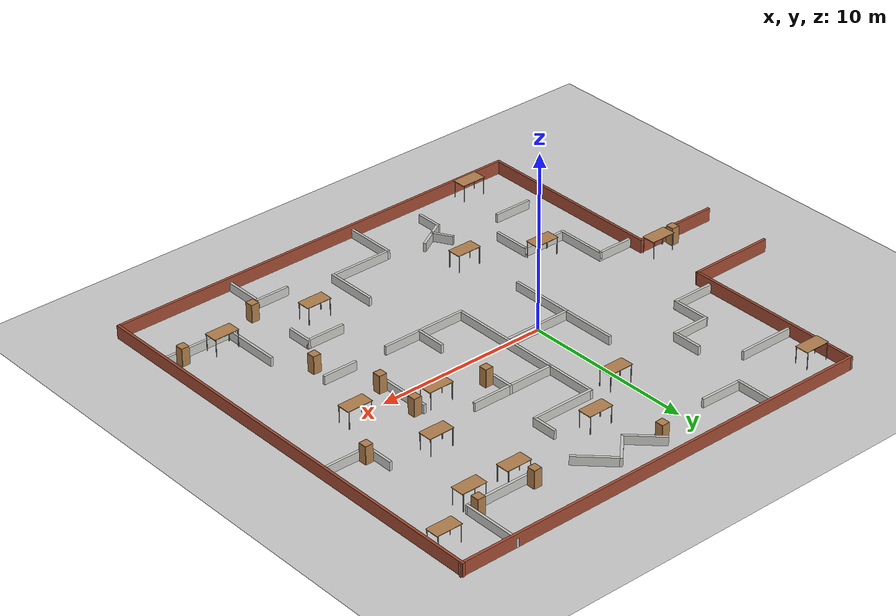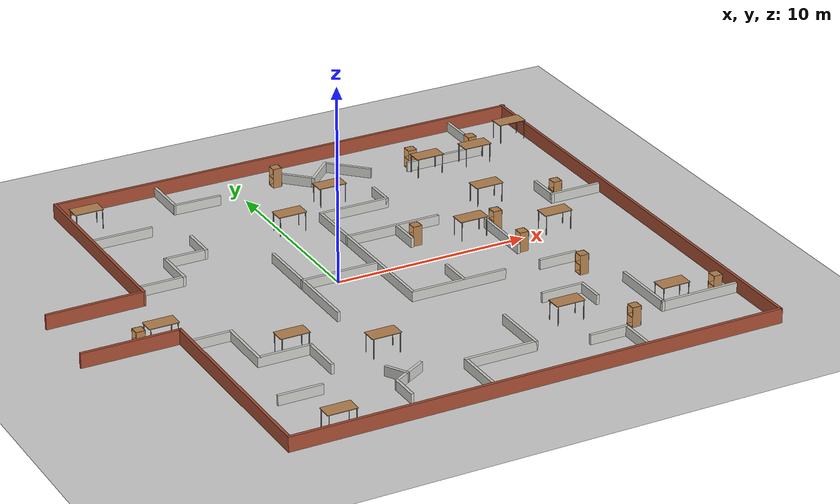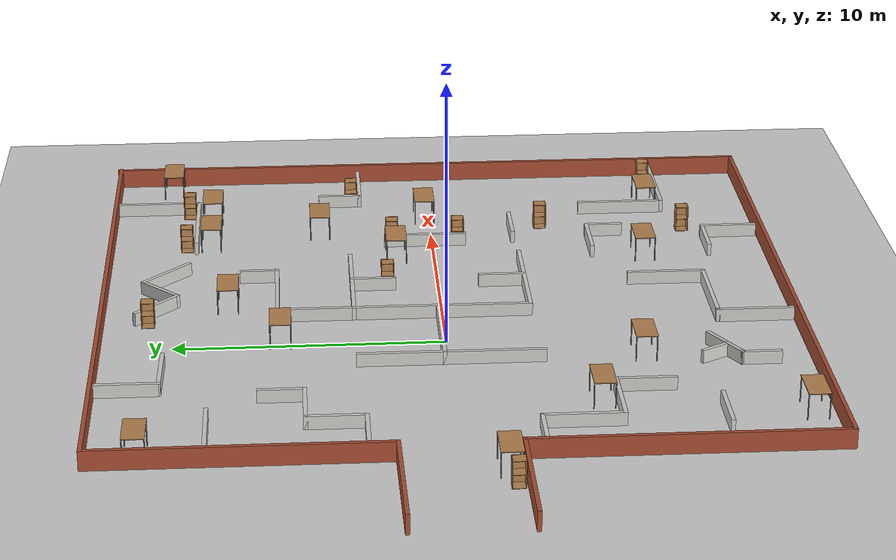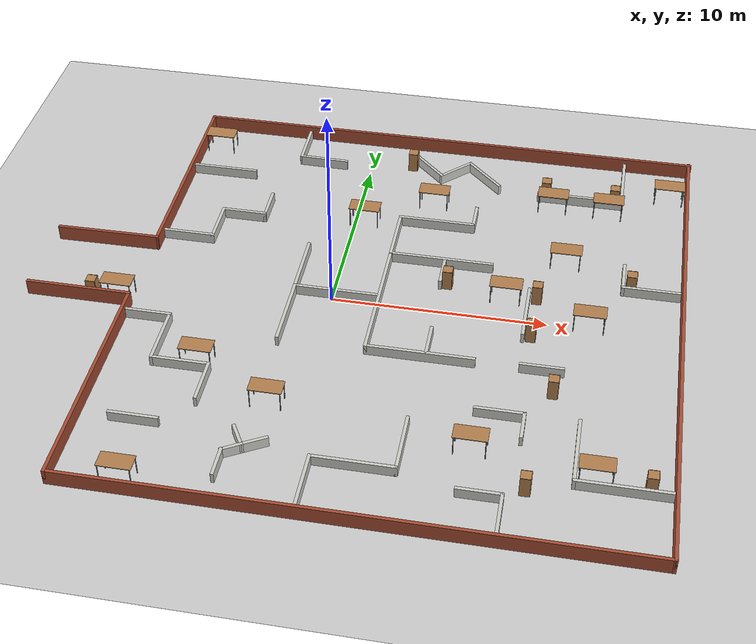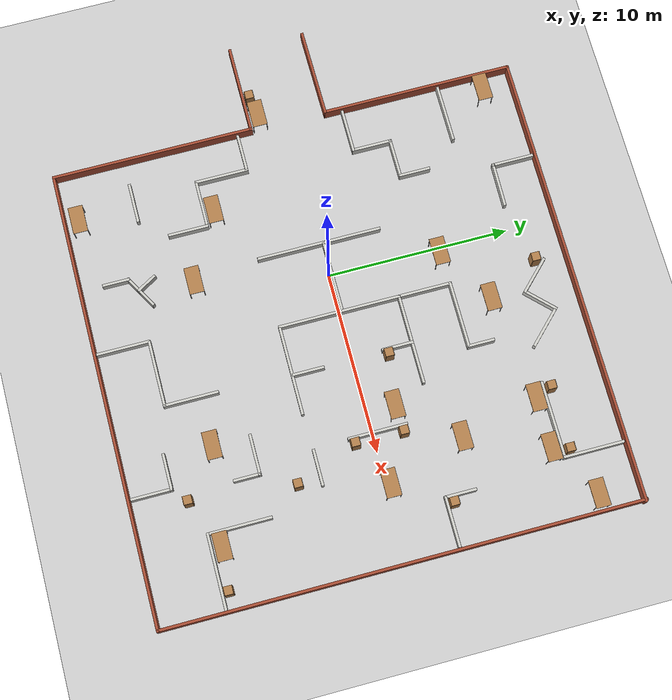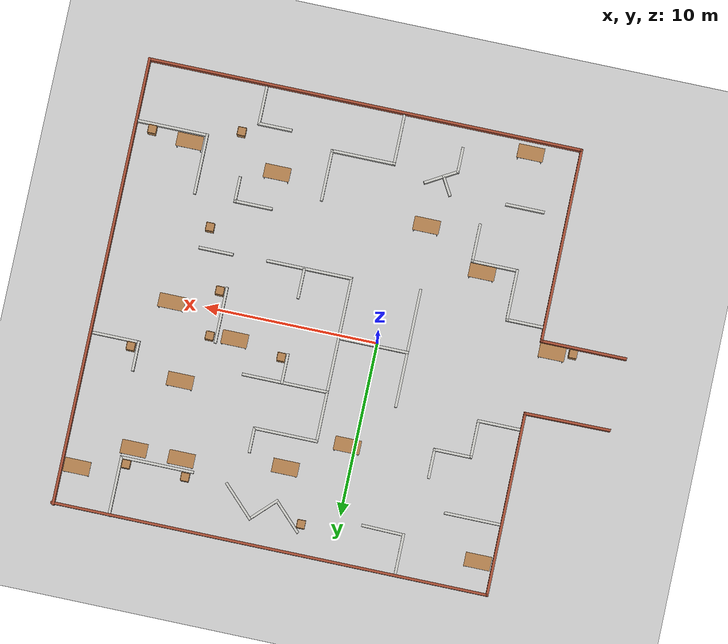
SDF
<sdf version="1.7">
 <world name="default">
  <light name="sun" type="directional">
   <pose>0 0 10 0 -0 0</pose>
   <diffuse>0.8 0.8 0.8 1</diffuse>
   <specular>0.2 0.2 0.2 1</specular>
   <attenuation>
    <range>1000</range>
    <constant>0.9</constant>
    <linear>0.01</linear>
    <quadratic>0.001</quadratic>
   </attenuation>
   <direction>-0.5 0.1 -0.9</direction>
   <spot><inner_angle>0</inner_angle><outer_angle>0</outer_angle><falloff>0</falloff></spot>
  </light>
  <gravity>0 0 -9.8</gravity>
  <magnetic_field>6e-06 2.3e-05 -4.2e-05</magnetic_field>
  <atmosphere type="adiabatic"/>
  <physics type="ode">
   <max_step_size>0.001</max_step_size>
   <real_time_factor>1</real_time_factor>
   <real_time_update_rate>1000</real_time_update_rate>
  </physics>
  <scene><ambient>0.4 0.4 0.4 1</ambient><background>0.7 0.7 0.7 1</background><shadows>1</shadows></scene>
  <spherical_coordinates>
   <surface_model>EARTH_WGS84</surface_model>
   <latitude_deg>0</latitude_deg>
   <longitude_deg>0</longitude_deg>
   <elevation>0</elevation>
   <heading_deg>0</heading_deg>
  </spherical_coordinates>
  <model name="ground_plane">
   <static>1</static>
   <link name="link">
    <collision name="collision">
     <geometry><plane><normal>0 0 1</normal><size>100 100</size></plane></geometry>
     <surface><friction><ode><mu>100</mu><mu2>50</mu2></ode></friction></surface>
    </collision>
    <visual name="visual">
     <cast_shadows>0</cast_shadows>
     <geometry><plane><normal>0 0 1</normal><size>100 100</size></plane></geometry>
     <material>
      <script><uri>file://media/materials/scripts/gazebo.material</uri><name>Gazebo/Grey</name></script>
     </material>
    </visual>
   </link>
  </model>
  <model name="mywall">
   <static>1</static>
   <pose>1.08 -0.208 0 0 -0 0</pose>
   <link name="Wall_10">
    <collision name="Wall_10_Collision">
     <geometry><box><size>11.25 0.15 0.75</size></box></geometry>
     <pose>0 0 0.375 0 -0 0</pose>
    </collision>
    <visual name="Wall_10_Visual">
     <pose>0 0 0.375 0 -0 0</pose>
     <geometry><box><size>11.25 0.15 0.75</size></box></geometry>
     <material>
      <script><uri>file://media/materials/scripts/gazebo.material</uri><name>Gazebo/Bricks</name></script>
      <ambient>1 1 1 1</ambient>
     </material>
     <meta><layer>0</layer></meta>
    </visual>
    <pose>-10.158 -7.375 0 0 -0 -1.5708</pose>
   </link>
   <link name="Wall_101">
    <collision name="Wall_101_Collision">
     <geometry><box><size>1.5 0.15 0.5</size></box></geometry>
     <pose>0 0 0.25 0 -0 0</pose>
    </collision>
    <visual name="Wall_101_Visual">
     <pose>0 0 0.25 0 -0 0</pose>
     <geometry><box><size>1.5 0.15 0.5</size></box></geometry>
     <material>
      <script><uri>file://media/materials/scripts/gazebo.material</uri><name>Gazebo/CeilingTiled</name></script>
      <ambient>1 1 1 1</ambient>
     </material>
     <meta><layer>0</layer></meta>
    </visual>
    <pose>-3.532 -10.96 0 0 -0 -1.5708</pose>
   </link>
   <link name="Wall_12">
    <collision name="Wall_12_Collision">
     <geometry><box><size>25.25 0.15 0.75</size></box></geometry>
     <pose>0 0 0.375 0 -0 0</pose>
    </collision>
    <visual name="Wall_12_Visual">
     <pose>0 0 0.375 0 -0 0</pose>
     <geometry><box><size>25.25 0.15 0.75</size></box></geometry>
     <material>
      <script><uri>file://media/materials/scripts/gazebo.material</uri><name>Gazebo/Bricks</name></script>
      <ambient>1 1 1 1</ambient>
     </material>
     <meta><layer>0</layer></meta>
    </visual>
    <pose>2.392 -12.925 0 0 -0 0</pose>
   </link>
   <link name="Wall_13">
    <collision name="Wall_13_Collision">
     <geometry><box><size>26 0.15 0.75</size></box></geometry>
     <pose>0 0 0.375 0 -0 0</pose>
    </collision>
    <visual name="Wall_13_Visual">
     <pose>0 0 0.375 0 -0 0</pose>
     <geometry><box><size>26 0.15 0.75</size></box></geometry>
     <material>
      <script><uri>file://media/materials/scripts/gazebo.material</uri><name>Gazebo/Bricks</name></script>
      <ambient>1 1 1 1</ambient>
     </material>
     <meta><layer>0</layer></meta>
    </visual>
    <pose>14.942 0 0 0 -0 1.5708</pose>
   </link>
   <link name="Wall_155">
    <collision name="Wall_155_Collision">
     <geometry><box><size>1.75 0.15 0.5</size></box></geometry>
     <pose>0 0 0.25 0 -0 0</pose>
    </collision>
    <visual name="Wall_155_Visual">
     <pose>0 0 0.25 0 -0 0</pose>
     <geometry><box><size>1.75 0.15 0.5</size></box></geometry>
     <material>
      <script><uri>file://media/materials/scripts/gazebo.material</uri><name>Gazebo/CeilingTiled</name></script>
      <ambient>1 1 1 1</ambient>
     </material>
     <meta><layer>0</layer></meta>
    </visual>
    <pose>3.846 -2.208 0 0 -0 1.5708</pose>
   </link>
   <link name="Wall_16">
    <collision name="Wall_16_Collision">
     <geometry><box><size>25.25 0.15 0.75</size></box></geometry>
     <pose>0 0 0.375 0 -0 0</pose>
    </collision>
    <visual name="Wall_16_Visual">
     <pose>0 0 0.375 0 -0 0</pose>
     <geometry><box><size>25.25 0.15 0.75</size></box></geometry>
     <material>
      <script><uri>file://media/materials/scripts/gazebo.material</uri><name>Gazebo/Bricks</name></script>
      <ambient>1 1 1 1</ambient>
     </material>
     <meta><layer>0</layer></meta>
    </visual>
    <pose>2.458 12.874 0 0 -0 0</pose>
   </link>
   <link name="Wall_18">
    <collision name="Wall_18_Collision">
     <geometry><box><size>2.5 0.15 0.5</size></box></geometry>
     <pose>0 0 0.25 0 -0 0</pose>
    </collision>
    <visual name="Wall_18_Visual">
     <pose>0 0 0.25 0 -0 0</pose>
     <geometry><box><size>2.5 0.15 0.5</size></box></geometry>
     <material>
      <script><uri>file://media/materials/scripts/gazebo.material</uri><name>Gazebo/CeilingTiled</name></script>
      <ambient>1 1 1 1</ambient>
     </material>
     <meta><layer>0</layer></meta>
    </visual>
    <pose>-8.778 3.333 0 0 -0 0</pose>
   </link>
   <link name="Wall_20">
    <collision name="Wall_20_Collision">
     <geometry><box><size>2.25 0.15 0.5</size></box></geometry>
     <pose>0 0 0.25 0 -0 0</pose>
    </collision>
    <visual name="Wall_20_Visual">
     <pose>0 0 0.25 0 -0 0</pose>
     <geometry><box><size>2.25 0.15 0.5</size></box></geometry>
     <material>
      <script><uri>file://media/materials/scripts/gazebo.material</uri><name>Gazebo/CeilingTiled</name></script>
      <ambient>1 1 1 1</ambient>
     </material>
     <meta><layer>0</layer></meta>
    </visual>
    <pose>-7.603 4.383 0 0 -0 1.5708</pose>
   </link>
   <link name="Wall_21">
    <collision name="Wall_21_Collision">
     <geometry><box><size>2.25 0.15 0.5</size></box></geometry>
     <pose>0 0 0.25 0 -0 0</pose>
    </collision>
    <visual name="Wall_21_Visual">
     <pose>0 0 0.25 0 -0 0</pose>
     <geometry><box><size>2.25 0.15 0.5</size></box></geometry>
     <material>
      <script><uri>file://media/materials/scripts/gazebo.material</uri><name>Gazebo/CeilingTiled</name></script>
      <ambient>1 1 1 1</ambient>
     </material>
     <meta><layer>0</layer></meta>
    </visual>
    <pose>-6.553 5.433 0 0 -0 0</pose>
   </link>
   <link name="Wall_22">
    <collision name="Wall_22_Collision">
     <geometry><box><size>1.75 0.15 0.5</size></box></geometry>
     <pose>0 0 0.25 0 -0 0</pose>
    </collision>
    <visual name="Wall_22_Visual">
     <pose>0 0 0.25 0 -0 0</pose>
     <geometry><box><size>1.75 0.15 0.5</size></box></geometry>
     <material>
      <script><uri>file://media/materials/scripts/gazebo.material</uri><name>Gazebo/CeilingTiled</name></script>
      <ambient>1 1 1 1</ambient>
     </material>
     <meta><layer>0</layer></meta>
    </visual>
    <pose>-5.503 6.233 0 0 -0 1.5708</pose>
   </link>
   <link name="Wall_24">
    <collision name="Wall_24_Collision">
     <geometry><box><size>2.25 0.15 0.5</size></box></geometry>
     <pose>0 0 0.25 0 -0 0</pose>
    </collision>
    <visual name="Wall_24_Visual">
     <pose>0 0 0.25 0 -0 0</pose>
     <geometry><box><size>2.25 0.15 0.5</size></box></geometry>
     <material>
      <script><uri>file://media/materials/scripts/gazebo.material</uri><name>Gazebo/CeilingTiled</name></script>
      <ambient>1 1 1 1</ambient>
     </material>
     <meta><layer>0</layer></meta>
    </visual>
    <pose>-9.042 -2.622 0 0 -0 0</pose>
   </link>
   <link name="Wall_25">
    <collision name="Wall_25_Collision">
     <geometry><box><size>3 0.15 0.5</size></box></geometry>
     <pose>0 0 0.25 0 -0 0</pose>
    </collision>
    <visual name="Wall_25_Visual">
     <pose>0 0 0.25 0 -0 0</pose>
     <geometry><box><size>3 0.15 0.5</size></box></geometry>
     <material>
      <script><uri>file://media/materials/scripts/gazebo.material</uri><name>Gazebo/CeilingTiled</name></script>
      <ambient>1 1 1 1</ambient>
     </material>
     <meta><layer>0</layer></meta>
    </visual>
    <pose>-7.992 -4.047 0 0 -0 -1.5708</pose>
   </link>
   <link name="Wall_26">
    <collision name="Wall_26_Collision">
     <geometry><box><size>2.75 0.15 0.5</size></box></geometry>
     <pose>0 0 0.25 0 -0 0</pose>
    </collision>
    <visual name="Wall_26_Visual">
     <pose>0 0 0.25 0 -0 0</pose>
     <geometry><box><size>2.75 0.15 0.5</size></box></geometry>
     <material>
      <script><uri>file://media/materials/scripts/gazebo.material</uri><name>Gazebo/CeilingTiled</name></script>
      <ambient>1 1 1 1</ambient>
     </material>
     <meta><layer>0</layer></meta>
    </visual>
    <pose>-6.692 -5.472 0 0 -0 0</pose>
   </link>
   <link name="Wall_27">
    <collision name="Wall_27_Collision">
     <geometry><box><size>2.25 0.15 0.5</size></box></geometry>
     <pose>0 0 0.25 0 -0 0</pose>
    </collision>
    <visual name="Wall_27_Visual">
     <pose>0 0 0.25 0 -0 0</pose>
     <geometry><box><size>2.25 0.15 0.5</size></box></geometry>
     <material>
      <script><uri>file://media/materials/scripts/gazebo.material</uri><name>Gazebo/CeilingTiled</name></script>
      <ambient>1 1 1 1</ambient>
     </material>
     <meta><layer>0</layer></meta>
    </visual>
    <pose>-5.392 -6.522 0 0 -0 -1.5708</pose>
   </link>
   <link name="Wall_29">
    <collision name="Wall_29_Collision">
     <geometry><box><size>2.25 0.15 0.5</size></box></geometry>
     <pose>0 0 0.25 0 -0 0</pose>
    </collision>
    <visual name="Wall_29_Visual">
     <pose>0 0 0.25 0 -0 0</pose>
     <geometry><box><size>2.25 0.15 0.5</size></box></geometry>
     <material>
      <script><uri>file://media/materials/scripts/gazebo.material</uri><name>Gazebo/CeilingTiled</name></script>
      <ambient>1 1 1 1</ambient>
     </material>
     <meta><layer>0</layer></meta>
    </visual>
    <pose>-7.693 -9.042 0 0 -0 0</pose>
   </link>
   <link name="Wall_3">
    <collision name="Wall_3_Collision">
     <geometry><box><size>5 0.15 0.75</size></box></geometry>
     <pose>0 0 0.375 0 -0 0</pose>
    </collision>
    <visual name="Wall_3_Visual">
     <pose>0 0 0.375 0 -0 0</pose>
     <geometry><box><size>5 0.15 0.75</size></box></geometry>
     <material>
      <script><uri>file://media/materials/scripts/gazebo.material</uri><name>Gazebo/Bricks</name></script>
      <ambient>1 1 1 1</ambient>
     </material>
     <meta><layer>0</layer></meta>
    </visual>
    <pose>-12.517 2.355 0 0 -0 0.011134</pose>
   </link>
   <link name="Wall_31">
    <collision name="Wall_31_Collision">
     <geometry><box><size>3.25 0.15 0.5</size></box></geometry>
     <pose>0 0 0.25 0 -0 0</pose>
    </collision>
    <visual name="Wall_31_Visual">
     <pose>0 0 0.25 0 -0 0</pose>
     <geometry><box><size>3.25 0.15 0.5</size></box></geometry>
     <material>
      <script><uri>file://media/materials/scripts/gazebo.material</uri><name>Gazebo/CeilingTiled</name></script>
      <ambient>1 1 1 1</ambient>
     </material>
     <meta><layer>0</layer></meta>
    </visual>
    <pose>-8.403 8.823 0 0 -0 0</pose>
   </link>
   <link name="Wall_33">
    <collision name="Wall_33_Collision">
     <geometry><box><size>6.75 0.15 0.5</size></box></geometry>
     <pose>0 0 0.25 0 -0 0</pose>
    </collision>
    <visual name="Wall_33_Visual">
     <pose>0 0 0.25 0 -0 0</pose>
     <geometry><box><size>6.75 0.15 0.5</size></box></geometry>
     <material>
      <script><uri>file://media/materials/scripts/gazebo.material</uri><name>Gazebo/CeilingTiled</name></script>
      <ambient>1 1 1 1</ambient>
     </material>
     <meta><layer>0</layer></meta>
    </visual>
    <pose>1.12 0.22 0 0 -0 -1.5708</pose>
   </link>
   <link name="Wall_34">
    <collision name="Wall_34_Collision">
     <geometry><box><size>5 0.15 0.5</size></box></geometry>
     <pose>0 0 0.25 0 -0 0</pose>
    </collision>
    <visual name="Wall_34_Visual">
     <pose>0 0 0.25 0 -0 0</pose>
     <geometry><box><size>5 0.15 0.5</size></box></geometry>
     <material>
      <script><uri>file://media/materials/scripts/gazebo.material</uri><name>Gazebo/CeilingTiled</name></script>
      <ambient>1 1 1 1</ambient>
     </material>
     <meta><layer>0</layer></meta>
    </visual>
    <pose>3.545 -3.08 0 0 -0 0</pose>
   </link>
   <link name="Wall_36">
    <collision name="Wall_36_Collision">
     <geometry><box><size>5 0.15 0.5</size></box></geometry>
     <pose>0 0 0.25 0 -0 0</pose>
    </collision>
    <visual name="Wall_36_Visual">
     <pose>0 0 0.25 0 -0 0</pose>
     <geometry><box><size>5 0.15 0.5</size></box></geometry>
     <material>
      <script><uri>file://media/materials/scripts/gazebo.material</uri><name>Gazebo/CeilingTiled</name></script>
      <ambient>1 1 1 1</ambient>
     </material>
     <meta><layer>0</layer></meta>
    </visual>
    <pose>3.545 3.52 0 0 -0 0</pose>
   </link>
   <link name="Wall_38">
    <collision name="Wall_38_Collision">
     <geometry><box><size>1.75 0.15 0.5</size></box></geometry>
     <pose>0 0 0.25 0 -0 0</pose>
    </collision>
    <visual name="Wall_38_Visual">
     <pose>0 0 0.25 0 -0 0</pose>
     <geometry><box><size>1.75 0.15 0.5</size></box></geometry>
     <material>
      <script><uri>file://media/materials/scripts/gazebo.material</uri><name>Gazebo/CeilingTiled</name></script>
      <ambient>1 1 1 1</ambient>
     </material>
     <meta><layer>0</layer></meta>
    </visual>
    <pose>3.741 2.72 0 0 -0 -1.5708</pose>
   </link>
   <link name="Wall_45">
    <collision name="Wall_45_Collision">
     <geometry><box><size>4.25 0.15 0.5</size></box></geometry>
     <pose>0 0 0.25 0 -0 0</pose>
    </collision>
    <visual name="Wall_45_Visual">
     <pose>0 0 0.25 0 -0 0</pose>
     <geometry><box><size>4.25 0.15 0.5</size></box></geometry>
     <material>
      <script><uri>file://media/materials/scripts/gazebo.material</uri><name>Gazebo/CeilingTiled</name></script>
      <ambient>1 1 1 1</ambient>
     </material>
     <meta><layer>0</layer></meta>
    </visual>
    <pose>12.888 -9.368 0 0 -0 3.14159</pose>
   </link>
   <link name="Wall_47">
    <collision name="Wall_47_Collision">
     <geometry><box><size>3.5 0.15 0.5</size></box></geometry>
     <pose>0 0 0.25 0 -0 0</pose>
    </collision>
    <visual name="Wall_47_Visual">
     <pose>0 0 0.25 0 -0 0</pose>
     <geometry><box><size>3.5 0.15 0.5</size></box></geometry>
     <material>
      <script><uri>file://media/materials/scripts/gazebo.material</uri><name>Gazebo/CeilingTiled</name></script>
      <ambient>1 1 1 1</ambient>
     </material>
     <meta><layer>0</layer></meta>
    </visual>
    <pose>10.838 -7.693 0 0 -0 1.5708</pose>
   </link>
   <link name="Wall_49">
    <collision name="Wall_49_Collision">
     <geometry><box><size>3.5 0.15 0.5</size></box></geometry>
     <pose>0 0 0.25 0 -0 0</pose>
    </collision>
    <visual name="Wall_49_Visual">
     <pose>0 0 0.25 0 -0 0</pose>
     <geometry><box><size>3.5 0.15 0.5</size></box></geometry>
     <material>
      <script><uri>file://media/materials/scripts/gazebo.material</uri><name>Gazebo/CeilingTiled</name></script>
      <ambient>1 1 1 1</ambient>
     </material>
     <meta><layer>0</layer></meta>
    </visual>
    <pose>11.728 11.213 0 0 -0 -1.5708</pose>
   </link>
   <link name="Wall_50">
    <collision name="Wall_50_Collision">
     <geometry><box><size>4.25 0.15 0.5</size></box></geometry>
     <pose>0 0 0.25 0 -0 0</pose>
    </collision>
    <visual name="Wall_50_Visual">
     <pose>0 0 0.25 0 -0 0</pose>
     <geometry><box><size>4.25 0.15 0.5</size></box></geometry>
     <material>
      <script><uri>file://media/materials/scripts/gazebo.material</uri><name>Gazebo/CeilingTiled</name></script>
      <ambient>1 1 1 1</ambient>
     </material>
     <meta><layer>0</layer></meta>
    </visual>
    <pose>9.678 9.538 0 0 -0 3.14159</pose>
   </link>
   <link name="Wall_52">
    <collision name="Wall_52_Collision">
     <geometry><box><size>3 0.15 0.5</size></box></geometry>
     <pose>0 0 0.25 0 -0 0</pose>
    </collision>
    <visual name="Wall_52_Visual">
     <pose>0 0 0.25 0 -0 0</pose>
     <geometry><box><size>3 0.15 0.5</size></box></geometry>
     <material>
      <script><uri>file://media/materials/scripts/gazebo.material</uri><name>Gazebo/CeilingTiled</name></script>
      <ambient>1 1 1 1</ambient>
     </material>
     <meta><layer>0</layer></meta>
    </visual>
    <pose>0.106 -11.404 0 0 -0 1.5708</pose>
   </link>
   <link name="Wall_54">
    <collision name="Wall_54_Collision">
     <geometry><box><size>3.75 0.15 0.5</size></box></geometry>
     <pose>0 0 0.25 0 -0 0</pose>
    </collision>
    <visual name="Wall_54_Visual">
     <pose>0 0 0.25 0 -0 0</pose>
     <geometry><box><size>3.75 0.15 0.5</size></box></geometry>
     <material>
      <script><uri>file://media/materials/scripts/gazebo.material</uri><name>Gazebo/CeilingTiled</name></script>
      <ambient>1 1 1 1</ambient>
     </material>
     <meta><layer>0</layer></meta>
    </visual>
    <pose>1.906 -9.979 0 0 -0 0</pose>
   </link>
   <link name="Wall_55">
    <collision name="Wall_55_Collision">
     <geometry><box><size>3 0.15 0.5</size></box></geometry>
     <pose>0 0 0.25 0 -0 0</pose>
    </collision>
    <visual name="Wall_55_Visual">
     <pose>0 0 0.25 0 -0 0</pose>
     <geometry><box><size>3 0.15 0.5</size></box></geometry>
     <material>
      <script><uri>file://media/materials/scripts/gazebo.material</uri><name>Gazebo/CeilingTiled</name></script>
      <ambient>1 1 1 1</ambient>
     </material>
     <meta><layer>0</layer></meta>
    </visual>
    <pose>3.706 -8.554 0 0 -0 1.5708</pose>
   </link>
   <link name="Wall_57">
    <collision name="Wall_57_Collision">
     <geometry><box><size>4 0.15 0.5</size></box></geometry>
     <pose>0 0 0.25 0 -0 0</pose>
    </collision>
    <visual name="Wall_57_Visual">
     <pose>0 0 0.25 0 -0 0</pose>
     <geometry><box><size>4 0.15 0.5</size></box></geometry>
     <material>
      <script><uri>file://media/materials/scripts/gazebo.material</uri><name>Gazebo/CeilingTiled</name></script>
      <ambient>1 1 1 1</ambient>
     </material>
     <meta><layer>0</layer></meta>
    </visual>
    <pose>-0.93 0.378 0 0 -0 3.14159</pose>
   </link>
   <link name="Wall_58">
    <collision name="Wall_58_Collision">
     <geometry><box><size>3.75 0.15 0.5</size></box></geometry>
     <pose>0 0 0.25 0 -0 0</pose>
    </collision>
    <visual name="Wall_58_Visual">
     <pose>0 0 0.25 0 -0 0</pose>
     <geometry><box><size>3.75 0.15 0.5</size></box></geometry>
     <material>
      <script><uri>file://media/materials/scripts/gazebo.material</uri><name>Gazebo/CeilingTiled</name></script>
      <ambient>1 1 1 1</ambient>
     </material>
     <meta><layer>0</layer></meta>
    </visual>
    <pose>-2.855 -1.422 0 0 -0 -1.5708</pose>
   </link>
   <link name="Wall_6">
    <collision name="Wall_6_Collision">
     <geometry><box><size>5 0.15 0.75</size></box></geometry>
     <pose>0 0 0.375 0 -0 0</pose>
    </collision>
    <visual name="Wall_6_Visual">
     <pose>0 0 0.375 0 -0 0</pose>
     <geometry><box><size>5 0.15 0.75</size></box></geometry>
     <material>
      <script><uri>file://media/materials/scripts/gazebo.material</uri><name>Gazebo/Bricks</name></script>
      <ambient>1 1 1 1</ambient>
     </material>
     <meta><layer>0</layer></meta>
    </visual>
    <pose>-12.583 -1.825 0 0 -0 0</pose>
   </link>
   <link name="Wall_60">
    <collision name="Wall_60_Collision">
     <geometry><box><size>3.25 0.15 0.5</size></box></geometry>
     <pose>0 0 0.25 0 -0 0</pose>
    </collision>
    <visual name="Wall_60_Visual">
     <pose>0 0 0.25 0 -0 0</pose>
     <geometry><box><size>3.25 0.15 0.5</size></box></geometry>
     <material>
      <script><uri>file://media/materials/scripts/gazebo.material</uri><name>Gazebo/CeilingTiled</name></script>
      <ambient>1 1 1 1</ambient>
     </material>
     <meta><layer>0</layer></meta>
    </visual>
    <pose>-2.855 1.928 0 0 -0 1.5708</pose>
   </link>
   <link name="Wall_62">
    <collision name="Wall_62_Collision">
     <geometry><box><size>2.25 0.15 0.5</size></box></geometry>
     <pose>0 0 0.25 0 -0 0</pose>
    </collision>
    <visual name="Wall_62_Visual">
     <pose>0 0 0.25 0 -0 0</pose>
     <geometry><box><size>2.25 0.15 0.5</size></box></geometry>
     <material>
      <script><uri>file://media/materials/scripts/gazebo.material</uri><name>Gazebo/CeilingTiled</name></script>
      <ambient>1 1 1 1</ambient>
     </material>
     <meta><layer>0</layer></meta>
    </visual>
    <pose>8.096 -11.686 0 0 -0 1.5708</pose>
   </link>
   <link name="Wall_63">
    <collision name="Wall_63_Collision">
     <geometry><box><size>2 0.15 0.5</size></box></geometry>
     <pose>0 0 0.25 0 -0 0</pose>
    </collision>
    <visual name="Wall_63_Visual">
     <pose>0 0 0.25 0 -0 0</pose>
     <geometry><box><size>2 0.15 0.5</size></box></geometry>
     <material>
      <script><uri>file://media/materials/scripts/gazebo.material</uri><name>Gazebo/CeilingTiled</name></script>
      <ambient>1 1 1 1</ambient>
     </material>
     <meta><layer>0</layer></meta>
    </visual>
    <pose>7.171 -10.636 0 0 -0 3.14159</pose>
   </link>
   <link name="Wall_65">
    <collision name="Wall_65_Collision">
     <geometry><box><size>1.25 0.15 0.5</size></box></geometry>
     <pose>0 0 0.25 0 -0 0</pose>
    </collision>
    <visual name="Wall_65_Visual">
     <pose>0 0 0.25 0 -0 0</pose>
     <geometry><box><size>1.25 0.15 0.5</size></box></geometry>
     <material>
      <script><uri>file://media/materials/scripts/gazebo.material</uri><name>Gazebo/CeilingTiled</name></script>
      <ambient>1 1 1 1</ambient>
     </material>
     <meta><layer>0</layer></meta>
    </visual>
    <pose>-3.07 -9.3835 0 0 -0 -1.04737</pose>
   </link>
   <link name="Wall_66">
    <collision name="Wall_66_Collision">
     <geometry><box><size>1.25 0.15 0.5</size></box></geometry>
     <pose>0 0 0.25 0 -0 0</pose>
    </collision>
    <visual name="Wall_66_Visual">
     <pose>0 0 0.25 0 -0 0</pose>
     <geometry><box><size>1.25 0.15 0.5</size></box></geometry>
     <material>
      <script><uri>file://media/materials/scripts/gazebo.material</uri><name>Gazebo/CeilingTiled</name></script>
      <ambient>1 1 1 1</ambient>
     </material>
     <meta><layer>0</layer></meta>
    </visual>
    <pose>-2.319 -9.585 0 0 -0 0.523884</pose>
   </link>
   <link name="Wall_68">
    <collision name="Wall_68_Collision">
     <geometry><box><size>1 0.15 0.5</size></box></geometry>
     <pose>0 0 0.25 0 -0 0</pose>
    </collision>
    <visual name="Wall_68_Visual">
     <pose>0 0 0.25 0 -0 0</pose>
     <geometry><box><size>1 0.15 0.5</size></box></geometry>
     <material>
      <script><uri>file://media/materials/scripts/gazebo.material</uri><name>Gazebo/CeilingTiled</name></script>
      <ambient>1 1 1 1</ambient>
     </material>
     <meta><layer>0</layer></meta>
    </visual>
    <pose>-3.1635 -10.0725 0 0 -0 -2.61851</pose>
   </link>
   <link name="Wall_71">
    <collision name="Wall_71_Collision">
     <geometry><box><size>3 0.15 0.5</size></box></geometry>
     <pose>0 0 0.25 0 -0 0</pose>
    </collision>
    <visual name="Wall_71_Visual">
     <pose>0 0 0.25 0 -0 0</pose>
     <geometry><box><size>3 0.15 0.5</size></box></geometry>
     <material>
      <script><uri>file://media/materials/scripts/gazebo.material</uri><name>Gazebo/CeilingTiled</name></script>
      <ambient>1 1 1 1</ambient>
     </material>
     <meta><layer>0</layer></meta>
    </visual>
    <pose>1.12 4.945 0 0 -0 1.5708</pose>
   </link>
   <link name="Wall_72">
    <collision name="Wall_72_Collision">
     <geometry><box><size>3.75 0.15 0.5</size></box></geometry>
     <pose>0 0 0.25 0 -0 0</pose>
    </collision>
    <visual name="Wall_72_Visual">
     <pose>0 0 0.25 0 -0 0</pose>
     <geometry><box><size>3.75 0.15 0.5</size></box></geometry>
     <material>
      <script><uri>file://media/materials/scripts/gazebo.material</uri><name>Gazebo/CeilingTiled</name></script>
      <ambient>1 1 1 1</ambient>
     </material>
     <meta><layer>0</layer></meta>
    </visual>
    <pose>2.92 6.37 0 0 -0 0</pose>
   </link>
   <link name="Wall_73">
    <collision name="Wall_73_Collision">
     <geometry><box><size>1.5 0.15 0.5</size></box></geometry>
     <pose>0 0 0.25 0 -0 0</pose>
    </collision>
    <visual name="Wall_73_Visual">
     <pose>0 0 0.25 0 -0 0</pose>
     <geometry><box><size>1.5 0.15 0.5</size></box></geometry>
     <material>
      <script><uri>file://media/materials/scripts/gazebo.material</uri><name>Gazebo/CeilingTiled</name></script>
      <ambient>1 1 1 1</ambient>
     </material>
     <meta><layer>0</layer></meta>
    </visual>
    <pose>4.72 7.045 0 0 -0 1.5708</pose>
   </link>
   <link name="Wall_75">
    <collision name="Wall_75_Collision">
     <geometry><box><size>2.75 0.15 0.5</size></box></geometry>
     <pose>0 0 0.25 0 -0 0</pose>
    </collision>
    <visual name="Wall_75_Visual">
     <pose>0 0 0.25 0 -0 0</pose>
     <geometry><box><size>2.75 0.15 0.5</size></box></geometry>
     <material>
      <script><uri>file://media/materials/scripts/gazebo.material</uri><name>Gazebo/CeilingTiled</name></script>
      <ambient>1 1 1 1</ambient>
     </material>
     <meta><layer>0</layer></meta>
    </visual>
    <pose>13.451 2.966 0 0 -0 3.14159</pose>
   </link>
   <link name="Wall_78">
    <collision name="Wall_78_Collision">
     <geometry><box><size>2.40642 0.15 0.5</size></box></geometry>
     <pose>0 0 0.25 0 -0 0</pose>
    </collision>
    <visual name="Wall_78_Visual">
     <pose>0 0 0.25 0 -0 0</pose>
     <geometry><box><size>2.40642 0.15 0.5</size></box></geometry>
     <material>
      <script><uri>file://media/materials/scripts/gazebo.material</uri><name>Gazebo/CeilingTiled</name></script>
      <ambient>1 1 1 1</ambient>
     </material>
     <meta><layer>0</layer></meta>
    </visual>
    <pose>-4.779 11.655 0 0 -0 -1.5708</pose>
   </link>
   <link name="Wall_79">
    <collision name="Wall_79_Collision">
     <geometry><box><size>2.5 0.15 0.5</size></box></geometry>
     <pose>0 0 0.25 0 -0 0</pose>
    </collision>
    <visual name="Wall_79_Visual">
     <pose>0 0 0.25 0 -0 0</pose>
     <geometry><box><size>2.5 0.15 0.5</size></box></geometry>
     <material>
      <script><uri>file://media/materials/scripts/gazebo.material</uri><name>Gazebo/CeilingTiled</name></script>
      <ambient>1 1 1 1</ambient>
     </material>
     <meta><layer>0</layer></meta>
    </visual>
    <pose>-3.604 10.5035 0 0 -0 -0.019997</pose>
   </link>
   <link name="Wall_8">
    <collision name="Wall_8_Collision">
     <geometry><box><size>10.6425 0.15 0.75</size></box></geometry>
     <pose>0 0 0.375 0 -0 0</pose>
    </collision>
    <visual name="Wall_8_Visual">
     <pose>0 0 0.375 0 -0 0</pose>
     <geometry><box><size>10.6425 0.15 0.75</size></box></geometry>
     <material>
      <script><uri>file://media/materials/scripts/gazebo.material</uri><name>Gazebo/Bricks</name></script>
      <ambient>1 1 1 1</ambient>
     </material>
     <meta><layer>0</layer></meta>
    </visual>
    <pose>-10.092 7.628 0 0 -0 1.5708</pose>
   </link>
   <link name="Wall_81">
    <collision name="Wall_81_Collision">
     <geometry><box><size>1.75 0.15 0.5</size></box></geometry>
     <pose>0 0 0.25 0 -0 0</pose>
    </collision>
    <visual name="Wall_81_Visual">
     <pose>0 0 0.25 0 -0 0</pose>
     <geometry><box><size>1.75 0.15 0.5</size></box></geometry>
     <material>
      <script><uri>file://media/materials/scripts/gazebo.material</uri><name>Gazebo/CeilingTiled</name></script>
      <ambient>1 1 1 1</ambient>
     </material>
     <meta><layer>0</layer></meta>
    </visual>
    <pose>12.151 3.766 0 0 -0 1.5708</pose>
   </link>
   <link name="Wall_84">
    <collision name="Wall_84_Collision">
     <geometry><box><size>3.25 0.15 0.5</size></box></geometry>
     <pose>0 0 0.25 0 -0 0</pose>
    </collision>
    <visual name="Wall_84_Visual">
     <pose>0 0 0.25 0 -0 0</pose>
     <geometry><box><size>3.25 0.15 0.5</size></box></geometry>
     <material>
      <script><uri>file://media/materials/scripts/gazebo.material</uri><name>Gazebo/CeilingTiled</name></script>
      <ambient>1 1 1 1</ambient>
     </material>
     <meta><layer>0</layer></meta>
    </visual>
    <pose>7.907 0.492 0 0 -0 -1.5708</pose>
   </link>
   <link name="Wall_86">
    <collision name="Wall_86_Collision">
     <geometry><box><size>2 0.15 0.5</size></box></geometry>
     <pose>0 0 0.25 0 -0 0</pose>
    </collision>
    <visual name="Wall_86_Visual">
     <pose>0 0 0.25 0 -0 0</pose>
     <geometry><box><size>2 0.15 0.5</size></box></geometry>
     <material>
      <script><uri>file://media/materials/scripts/gazebo.material</uri><name>Gazebo/CeilingTiled</name></script>
      <ambient>1 1 1 1</ambient>
     </material>
     <meta><layer>0</layer></meta>
    </visual>
    <pose>8.956 -3.013 0 0 -0 0</pose>
   </link>
   <link name="Wall_88">
    <collision name="Wall_88_Collision">
     <geometry><box><size>2.25 0.15 0.5</size></box></geometry>
     <pose>0 0 0.25 0 -0 0</pose>
    </collision>
    <visual name="Wall_88_Visual">
     <pose>0 0 0.25 0 -0 0</pose>
     <geometry><box><size>2.25 0.15 0.5</size></box></geometry>
     <material>
      <script><uri>file://media/materials/scripts/gazebo.material</uri><name>Gazebo/CeilingTiled</name></script>
      <ambient>1 1 1 1</ambient>
     </material>
     <meta><layer>0</layer></meta>
    </visual>
    <pose>7.454 -6.021 0 0 -0 0</pose>
   </link>
   <link name="Wall_89">
    <collision name="Wall_89_Collision">
     <geometry><box><size>1.5 0.15 0.5</size></box></geometry>
     <pose>0 0 0.25 0 -0 0</pose>
    </collision>
    <visual name="Wall_89_Visual">
     <pose>0 0 0.25 0 -0 0</pose>
     <geometry><box><size>1.5 0.15 0.5</size></box></geometry>
     <material>
      <script><uri>file://media/materials/scripts/gazebo.material</uri><name>Gazebo/CeilingTiled</name></script>
      <ambient>1 1 1 1</ambient>
     </material>
     <meta><layer>0</layer></meta>
    </visual>
    <pose>8.504 -6.696 0 0 -0 -1.5708</pose>
   </link>
   <link name="Wall_95">
    <collision name="Wall_95_Collision">
     <geometry><box><size>2.25 0.15 0.5</size></box></geometry>
     <pose>0 0 0.25 0 -0 0</pose>
    </collision>
    <visual name="Wall_95_Visual">
     <pose>0 0 0.25 0 -0 0</pose>
     <geometry><box><size>2.25 0.15 0.5</size></box></geometry>
     <material>
      <script><uri>file://media/materials/scripts/gazebo.material</uri><name>Gazebo/CeilingTiled</name></script>
      <ambient>1 1 1 1</ambient>
     </material>
     <meta><layer>0</layer></meta>
    </visual>
    <pose>1.8635 10.8755 0 0 -0 -0.785398</pose>
   </link>
   <link name="Wall_96">
    <collision name="Wall_96_Collision">
     <geometry><box><size>2 0.15 0.5</size></box></geometry>
     <pose>0 0 0.25 0 -0 0</pose>
    </collision>
    <visual name="Wall_96_Visual">
     <pose>0 0 0.25 0 -0 0</pose>
     <geometry><box><size>2 0.15 0.5</size></box></geometry>
     <material>
      <script><uri>file://media/materials/scripts/gazebo.material</uri><name>Gazebo/CeilingTiled</name></script>
      <ambient>1 1 1 1</ambient>
     </material>
     <meta><layer>0</layer></meta>
    </visual>
    <pose>3.26 10.787 0 0 -0 0.785398</pose>
   </link>
   <link name="Wall_97">
    <collision name="Wall_97_Collision">
     <geometry><box><size>2.5 0.15 0.5</size></box></geometry>
     <pose>0 0 0.25 0 -0 0</pose>
    </collision>
    <visual name="Wall_97_Visual">
     <pose>0 0 0.25 0 -0 0</pose>
     <geometry><box><size>2.5 0.15 0.5</size></box></geometry>
     <material>
      <script><uri>file://media/materials/scripts/gazebo.material</uri><name>Gazebo/CeilingTiled</name></script>
      <ambient>1 1 1 1</ambient>
     </material>
     <meta><layer>0</layer></meta>
    </visual>
    <pose>4.745 10.61 0 0 -0 -0.785398</pose>
   </link>
   <static>1</static>
  </model>
  <model name="table">
   <static>1</static>
   <link name="link">
    <collision name="surface">
     <pose>0 0 1 0 -0 0</pose>
     <geometry><box><size>1.5 0.8 0.03</size></box></geometry>
     <surface><friction><ode><mu>0.6</mu><mu2>0.6</mu2></ode></friction></surface>
    </collision>
    <visual name="visual1">
     <pose>0 0 1 0 -0 0</pose>
     <geometry><box><size>1.5 0.8 0.03</size></box></geometry>
     <material>
      <script><uri>file://media/materials/scripts/gazebo.material</uri><name>Gazebo/Wood</name></script>
     </material>
    </visual>
    <collision name="front_left_leg">
     <pose>0.68 0.38 0.5 0 -0 0</pose>
     <geometry><cylinder><radius>0.02</radius><length>1</length></cylinder></geometry>
    </collision>
    <visual name="front_left_leg">
     <pose>0.68 0.38 0.5 0 -0 0</pose>
     <geometry><cylinder><radius>0.02</radius><length>1</length></cylinder></geometry>
     <material>
      <script><uri>file://media/materials/scripts/gazebo.material</uri><name>Gazebo/Grey</name></script>
     </material>
    </visual>
    <collision name="front_right_leg">
     <pose>0.68 -0.38 0.5 0 -0 0</pose>
     <geometry><cylinder><radius>0.02</radius><length>1</length></cylinder></geometry>
    </collision>
    <visual name="front_right_leg">
     <pose>0.68 -0.38 0.5 0 -0 0</pose>
     <geometry><cylinder><radius>0.02</radius><length>1</length></cylinder></geometry>
     <material>
      <script><uri>file://media/materials/scripts/gazebo.material</uri><name>Gazebo/Grey</name></script>
     </material>
    </visual>
    <collision name="back_right_leg">
     <pose>-0.68 -0.38 0.5 0 -0 0</pose>
     <geometry><cylinder><radius>0.02</radius><length>1</length></cylinder></geometry>
    </collision>
    <visual name="back_right_leg">
     <pose>-0.68 -0.38 0.5 0 -0 0</pose>
     <geometry><cylinder><radius>0.02</radius><length>1</length></cylinder></geometry>
     <material>
      <script><uri>file://media/materials/scripts/gazebo.material</uri><name>Gazebo/Grey</name></script>
     </material>
    </visual>
    <collision name="back_left_leg">
     <pose>-0.68 0.38 0.5 0 -0 0</pose>
     <geometry><cylinder><radius>0.02</radius><length>1</length></cylinder></geometry>
    </collision>
    <visual name="back_left_leg">
     <pose>-0.68 0.38 0.5 0 -0 0</pose>
     <geometry><cylinder><radius>0.02</radius><length>1</length></cylinder></geometry>
     <material>
      <script><uri>file://media/materials/scripts/gazebo.material</uri><name>Gazebo/Grey</name></script>
     </material>
    </visual>
   </link>
   <pose>-4.9723 -5.12914 0 0 -0 0</pose>
  </model>
  <model name="table_clone">
   <static>1</static>
   <link name="link">
    <collision name="surface">
     <pose>0 0 1 0 -0 0</pose>
     <geometry><box><size>1.5 0.8 0.03</size></box></geometry>
     <surface><friction><ode><mu>0.6</mu><mu2>0.6</mu2></ode></friction></surface>
    </collision>
    <visual name="visual1">
     <pose>0 0 1 0 -0 0</pose>
     <geometry><box><size>1.5 0.8 0.03</size></box></geometry>
     <material>
      <script><uri>file://media/materials/scripts/gazebo.material</uri><name>Gazebo/Wood</name></script>
     </material>
    </visual>
    <collision name="front_left_leg">
     <pose>0.68 0.38 0.5 0 -0 0</pose>
     <geometry><cylinder><radius>0.02</radius><length>1</length></cylinder></geometry>
    </collision>
    <visual name="front_left_leg">
     <pose>0.68 0.38 0.5 0 -0 0</pose>
     <geometry><cylinder><radius>0.02</radius><length>1</length></cylinder></geometry>
     <material>
      <script><uri>file://media/materials/scripts/gazebo.material</uri><name>Gazebo/Grey</name></script>
     </material>
    </visual>
    <collision name="front_right_leg">
     <pose>0.68 -0.38 0.5 0 -0 0</pose>
     <geometry><cylinder><radius>0.02</radius><length>1</length></cylinder></geometry>
    </collision>
    <visual name="front_right_leg">
     <pose>0.68 -0.38 0.5 0 -0 0</pose>
     <geometry><cylinder><radius>0.02</radius><length>1</length></cylinder></geometry>
     <material>
      <script><uri>file://media/materials/scripts/gazebo.material</uri><name>Gazebo/Grey</name></script>
     </material>
    </visual>
    <collision name="back_right_leg">
     <pose>-0.68 -0.38 0.5 0 -0 0</pose>
     <geometry><cylinder><radius>0.02</radius><length>1</length></cylinder></geometry>
    </collision>
    <visual name="back_right_leg">
     <pose>-0.68 -0.38 0.5 0 -0 0</pose>
     <geometry><cylinder><radius>0.02</radius><length>1</length></cylinder></geometry>
     <material>
      <script><uri>file://media/materials/scripts/gazebo.material</uri><name>Gazebo/Grey</name></script>
     </material>
    </visual>
    <collision name="back_left_leg">
     <pose>-0.68 0.38 0.5 0 -0 0</pose>
     <geometry><cylinder><radius>0.02</radius><length>1</length></cylinder></geometry>
    </collision>
    <visual name="back_left_leg">
     <pose>-0.68 0.38 0.5 0 -0 0</pose>
     <geometry><cylinder><radius>0.02</radius><length>1</length></cylinder></geometry>
     <material>
      <script><uri>file://media/materials/scripts/gazebo.material</uri><name>Gazebo/Grey</name></script>
     </material>
    </visual>
   </link>
   <pose>0.444459 6.05097 0 0 -0 0</pose>
  </model>
  <model name="table_clone_clone">
   <static>1</static>
   <link name="link">
    <collision name="surface">
     <pose>0 0 1 0 -0 0</pose>
     <geometry><box><size>1.5 0.8 0.03</size></box></geometry>
     <surface><friction><ode><mu>0.6</mu><mu2>0.6</mu2></ode></friction></surface>
    </collision>
    <visual name="visual1">
     <pose>0 0 1 0 -0 0</pose>
     <geometry><box><size>1.5 0.8 0.03</size></box></geometry>
     <material>
      <script><uri>file://media/materials/scripts/gazebo.material</uri><name>Gazebo/Wood</name></script>
     </material>
    </visual>
    <collision name="front_left_leg">
     <pose>0.68 0.38 0.5 0 -0 0</pose>
     <geometry><cylinder><radius>0.02</radius><length>1</length></cylinder></geometry>
    </collision>
    <visual name="front_left_leg">
     <pose>0.68 0.38 0.5 0 -0 0</pose>
     <geometry><cylinder><radius>0.02</radius><length>1</length></cylinder></geometry>
     <material>
      <script><uri>file://media/materials/scripts/gazebo.material</uri><name>Gazebo/Grey</name></script>
     </material>
    </visual>
    <collision name="front_right_leg">
     <pose>0.68 -0.38 0.5 0 -0 0</pose>
     <geometry><cylinder><radius>0.02</radius><length>1</length></cylinder></geometry>
    </collision>
    <visual name="front_right_leg">
     <pose>0.68 -0.38 0.5 0 -0 0</pose>
     <geometry><cylinder><radius>0.02</radius><length>1</length></cylinder></geometry>
     <material>
      <script><uri>file://media/materials/scripts/gazebo.material</uri><name>Gazebo/Grey</name></script>
     </material>
    </visual>
    <collision name="back_right_leg">
     <pose>-0.68 -0.38 0.5 0 -0 0</pose>
     <geometry><cylinder><radius>0.02</radius><length>1</length></cylinder></geometry>
    </collision>
    <visual name="back_right_leg">
     <pose>-0.68 -0.38 0.5 0 -0 0</pose>
     <geometry><cylinder><radius>0.02</radius><length>1</length></cylinder></geometry>
     <material>
      <script><uri>file://media/materials/scripts/gazebo.material</uri><name>Gazebo/Grey</name></script>
     </material>
    </visual>
    <collision name="back_left_leg">
     <pose>-0.68 0.38 0.5 0 -0 0</pose>
     <geometry><cylinder><radius>0.02</radius><length>1</length></cylinder></geometry>
    </collision>
    <visual name="back_left_leg">
     <pose>-0.68 0.38 0.5 0 -0 0</pose>
     <geometry><cylinder><radius>0.02</radius><length>1</length></cylinder></geometry>
     <material>
      <script><uri>file://media/materials/scripts/gazebo.material</uri><name>Gazebo/Grey</name></script>
     </material>
    </visual>
   </link>
   <pose>-8.10257 10.9314 0 0 -0 0</pose>
  </model>
  <model name="table_clone_0">
   <static>1</static>
   <link name="link">
    <collision name="surface">
     <pose>0 0 1 0 -0 0</pose>
     <geometry><box><size>1.5 0.8 0.03</size></box></geometry>
     <surface><friction><ode><mu>0.6</mu><mu2>0.6</mu2></ode></friction></surface>
    </collision>
    <visual name="visual1">
     <pose>0 0 1 0 -0 0</pose>
     <geometry><box><size>1.5 0.8 0.03</size></box></geometry>
     <material>
      <script><uri>file://media/materials/scripts/gazebo.material</uri><name>Gazebo/Wood</name></script>
     </material>
    </visual>
    <collision name="front_left_leg">
     <pose>0.68 0.38 0.5 0 -0 0</pose>
     <geometry><cylinder><radius>0.02</radius><length>1</length></cylinder></geometry>
    </collision>
    <visual name="front_left_leg">
     <pose>0.68 0.38 0.5 0 -0 0</pose>
     <geometry><cylinder><radius>0.02</radius><length>1</length></cylinder></geometry>
     <material>
      <script><uri>file://media/materials/scripts/gazebo.material</uri><name>Gazebo/Grey</name></script>
     </material>
    </visual>
    <collision name="front_right_leg">
     <pose>0.68 -0.38 0.5 0 -0 0</pose>
     <geometry><cylinder><radius>0.02</radius><length>1</length></cylinder></geometry>
    </collision>
    <visual name="front_right_leg">
     <pose>0.68 -0.38 0.5 0 -0 0</pose>
     <geometry><cylinder><radius>0.02</radius><length>1</length></cylinder></geometry>
     <material>
      <script><uri>file://media/materials/scripts/gazebo.material</uri><name>Gazebo/Grey</name></script>
     </material>
    </visual>
    <collision name="back_right_leg">
     <pose>-0.68 -0.38 0.5 0 -0 0</pose>
     <geometry><cylinder><radius>0.02</radius><length>1</length></cylinder></geometry>
    </collision>
    <visual name="back_right_leg">
     <pose>-0.68 -0.38 0.5 0 -0 0</pose>
     <geometry><cylinder><radius>0.02</radius><length>1</length></cylinder></geometry>
     <material>
      <script><uri>file://media/materials/scripts/gazebo.material</uri><name>Gazebo/Grey</name></script>
     </material>
    </visual>
    <collision name="back_left_leg">
     <pose>-0.68 0.38 0.5 0 -0 0</pose>
     <geometry><cylinder><radius>0.02</radius><length>1</length></cylinder></geometry>
    </collision>
    <visual name="back_left_leg">
     <pose>-0.68 0.38 0.5 0 -0 0</pose>
     <geometry><cylinder><radius>0.02</radius><length>1</length></cylinder></geometry>
     <material>
      <script><uri>file://media/materials/scripts/gazebo.material</uri><name>Gazebo/Grey</name></script>
     </material>
    </visual>
   </link>
   <pose>-1.35096 -7.07816 0 0 -0 0</pose>
  </model>
  <model name="table_clone_1">
   <static>1</static>
   <link name="link">
    <collision name="surface">
     <pose>0 0 1 0 -0 0</pose>
     <geometry><box><size>1.5 0.8 0.03</size></box></geometry>
     <surface><friction><ode><mu>0.6</mu><mu2>0.6</mu2></ode></friction></surface>
    </collision>
    <visual name="visual1">
     <pose>0 0 1 0 -0 0</pose>
     <geometry><box><size>1.5 0.8 0.03</size></box></geometry>
     <material>
      <script><uri>file://media/materials/scripts/gazebo.material</uri><name>Gazebo/Wood</name></script>
     </material>
    </visual>
    <collision name="front_left_leg">
     <pose>0.68 0.38 0.5 0 -0 0</pose>
     <geometry><cylinder><radius>0.02</radius><length>1</length></cylinder></geometry>
    </collision>
    <visual name="front_left_leg">
     <pose>0.68 0.38 0.5 0 -0 0</pose>
     <geometry><cylinder><radius>0.02</radius><length>1</length></cylinder></geometry>
     <material>
      <script><uri>file://media/materials/scripts/gazebo.material</uri><name>Gazebo/Grey</name></script>
     </material>
    </visual>
    <collision name="front_right_leg">
     <pose>0.68 -0.38 0.5 0 -0 0</pose>
     <geometry><cylinder><radius>0.02</radius><length>1</length></cylinder></geometry>
    </collision>
    <visual name="front_right_leg">
     <pose>0.68 -0.38 0.5 0 -0 0</pose>
     <geometry><cylinder><radius>0.02</radius><length>1</length></cylinder></geometry>
     <material>
      <script><uri>file://media/materials/scripts/gazebo.material</uri><name>Gazebo/Grey</name></script>
     </material>
    </visual>
    <collision name="back_right_leg">
     <pose>-0.68 -0.38 0.5 0 -0 0</pose>
     <geometry><cylinder><radius>0.02</radius><length>1</length></cylinder></geometry>
    </collision>
    <visual name="back_right_leg">
     <pose>-0.68 -0.38 0.5 0 -0 0</pose>
     <geometry><cylinder><radius>0.02</radius><length>1</length></cylinder></geometry>
     <material>
      <script><uri>file://media/materials/scripts/gazebo.material</uri><name>Gazebo/Grey</name></script>
     </material>
    </visual>
    <collision name="back_left_leg">
     <pose>-0.68 0.38 0.5 0 -0 0</pose>
     <geometry><cylinder><radius>0.02</radius><length>1</length></cylinder></geometry>
    </collision>
    <visual name="back_left_leg">
     <pose>-0.68 0.38 0.5 0 -0 0</pose>
     <geometry><cylinder><radius>0.02</radius><length>1</length></cylinder></geometry>
     <material>
      <script><uri>file://media/materials/scripts/gazebo.material</uri><name>Gazebo/Grey</name></script>
     </material>
    </visual>
   </link>
   <pose>3.6038 8.0012 0 0 -0 0</pose>
  </model>
  <model name="table_clone_2">
   <static>1</static>
   <link name="link">
    <collision name="surface">
     <pose>0 0 1 0 -0 0</pose>
     <geometry><box><size>1.5 0.8 0.03</size></box></geometry>
     <surface><friction><ode><mu>0.6</mu><mu2>0.6</mu2></ode></friction></surface>
    </collision>
    <visual name="visual1">
     <pose>0 0 1 0 -0 0</pose>
     <geometry><box><size>1.5 0.8 0.03</size></box></geometry>
     <material>
      <script><uri>file://media/materials/scripts/gazebo.material</uri><name>Gazebo/Wood</name></script>
     </material>
    </visual>
    <collision name="front_left_leg">
     <pose>0.68 0.38 0.5 0 -0 0</pose>
     <geometry><cylinder><radius>0.02</radius><length>1</length></cylinder></geometry>
    </collision>
    <visual name="front_left_leg">
     <pose>0.68 0.38 0.5 0 -0 0</pose>
     <geometry><cylinder><radius>0.02</radius><length>1</length></cylinder></geometry>
     <material>
      <script><uri>file://media/materials/scripts/gazebo.material</uri><name>Gazebo/Grey</name></script>
     </material>
    </visual>
    <collision name="front_right_leg">
     <pose>0.68 -0.38 0.5 0 -0 0</pose>
     <geometry><cylinder><radius>0.02</radius><length>1</length></cylinder></geometry>
    </collision>
    <visual name="front_right_leg">
     <pose>0.68 -0.38 0.5 0 -0 0</pose>
     <geometry><cylinder><radius>0.02</radius><length>1</length></cylinder></geometry>
     <material>
      <script><uri>file://media/materials/scripts/gazebo.material</uri><name>Gazebo/Grey</name></script>
     </material>
    </visual>
    <collision name="back_right_leg">
     <pose>-0.68 -0.38 0.5 0 -0 0</pose>
     <geometry><cylinder><radius>0.02</radius><length>1</length></cylinder></geometry>
    </collision>
    <visual name="back_right_leg">
     <pose>-0.68 -0.38 0.5 0 -0 0</pose>
     <geometry><cylinder><radius>0.02</radius><length>1</length></cylinder></geometry>
     <material>
      <script><uri>file://media/materials/scripts/gazebo.material</uri><name>Gazebo/Grey</name></script>
     </material>
    </visual>
    <collision name="back_left_leg">
     <pose>-0.68 0.38 0.5 0 -0 0</pose>
     <geometry><cylinder><radius>0.02</radius><length>1</length></cylinder></geometry>
    </collision>
    <visual name="back_left_leg">
     <pose>-0.68 0.38 0.5 0 -0 0</pose>
     <geometry><cylinder><radius>0.02</radius><length>1</length></cylinder></geometry>
     <material>
      <script><uri>file://media/materials/scripts/gazebo.material</uri><name>Gazebo/Grey</name></script>
     </material>
    </visual>
   </link>
   <pose>-6.27569 -12.3411 0 0 -0 0</pose>
  </model>
  <model name="table_clone_1_clone">
   <static>1</static>
   <link name="link">
    <collision name="surface">
     <pose>0 0 1 0 -0 0</pose>
     <geometry><box><size>1.5 0.8 0.03</size></box></geometry>
     <surface><friction><ode><mu>0.6</mu><mu2>0.6</mu2></ode></friction></surface>
    </collision>
    <visual name="visual1">
     <pose>0 0 1 0 -0 0</pose>
     <geometry><box><size>1.5 0.8 0.03</size></box></geometry>
     <material>
      <script><uri>file://media/materials/scripts/gazebo.material</uri><name>Gazebo/Wood</name></script>
     </material>
    </visual>
    <collision name="front_left_leg">
     <pose>0.68 0.38 0.5 0 -0 0</pose>
     <geometry><cylinder><radius>0.02</radius><length>1</length></cylinder></geometry>
    </collision>
    <visual name="front_left_leg">
     <pose>0.68 0.38 0.5 0 -0 0</pose>
     <geometry><cylinder><radius>0.02</radius><length>1</length></cylinder></geometry>
     <material>
      <script><uri>file://media/materials/scripts/gazebo.material</uri><name>Gazebo/Grey</name></script>
     </material>
    </visual>
    <collision name="front_right_leg">
     <pose>0.68 -0.38 0.5 0 -0 0</pose>
     <geometry><cylinder><radius>0.02</radius><length>1</length></cylinder></geometry>
    </collision>
    <visual name="front_right_leg">
     <pose>0.68 -0.38 0.5 0 -0 0</pose>
     <geometry><cylinder><radius>0.02</radius><length>1</length></cylinder></geometry>
     <material>
      <script><uri>file://media/materials/scripts/gazebo.material</uri><name>Gazebo/Grey</name></script>
     </material>
    </visual>
    <collision name="back_right_leg">
     <pose>-0.68 -0.38 0.5 0 -0 0</pose>
     <geometry><cylinder><radius>0.02</radius><length>1</length></cylinder></geometry>
    </collision>
    <visual name="back_right_leg">
     <pose>-0.68 -0.38 0.5 0 -0 0</pose>
     <geometry><cylinder><radius>0.02</radius><length>1</length></cylinder></geometry>
     <material>
      <script><uri>file://media/materials/scripts/gazebo.material</uri><name>Gazebo/Grey</name></script>
     </material>
    </visual>
    <collision name="back_left_leg">
     <pose>-0.68 0.38 0.5 0 -0 0</pose>
     <geometry><cylinder><radius>0.02</radius><length>1</length></cylinder></geometry>
    </collision>
    <visual name="back_left_leg">
     <pose>-0.68 0.38 0.5 0 -0 0</pose>
     <geometry><cylinder><radius>0.02</radius><length>1</length></cylinder></geometry>
     <material>
      <script><uri>file://media/materials/scripts/gazebo.material</uri><name>Gazebo/Grey</name></script>
     </material>
    </visual>
   </link>
   <pose>9.45234 8.75079 0 0 -0 0</pose>
  </model>
  <model name="table_clone_1_clone_0">
   <static>1</static>
   <link name="link">
    <collision name="surface">
     <pose>0 0 1 0 -0 0</pose>
     <geometry><box><size>1.5 0.8 0.03</size></box></geometry>
     <surface><friction><ode><mu>0.6</mu><mu2>0.6</mu2></ode></friction></surface>
    </collision>
    <visual name="visual1">
     <pose>0 0 1 0 -0 0</pose>
     <geometry><box><size>1.5 0.8 0.03</size></box></geometry>
     <material>
      <script><uri>file://media/materials/scripts/gazebo.material</uri><name>Gazebo/Wood</name></script>
     </material>
    </visual>
    <collision name="front_left_leg">
     <pose>0.68 0.38 0.5 0 -0 0</pose>
     <geometry><cylinder><radius>0.02</radius><length>1</length></cylinder></geometry>
    </collision>
    <visual name="front_left_leg">
     <pose>0.68 0.38 0.5 0 -0 0</pose>
     <geometry><cylinder><radius>0.02</radius><length>1</length></cylinder></geometry>
     <material>
      <script><uri>file://media/materials/scripts/gazebo.material</uri><name>Gazebo/Grey</name></script>
     </material>
    </visual>
    <collision name="front_right_leg">
     <pose>0.68 -0.38 0.5 0 -0 0</pose>
     <geometry><cylinder><radius>0.02</radius><length>1</length></cylinder></geometry>
    </collision>
    <visual name="front_right_leg">
     <pose>0.68 -0.38 0.5 0 -0 0</pose>
     <geometry><cylinder><radius>0.02</radius><length>1</length></cylinder></geometry>
     <material>
      <script><uri>file://media/materials/scripts/gazebo.material</uri><name>Gazebo/Grey</name></script>
     </material>
    </visual>
    <collision name="back_right_leg">
     <pose>-0.68 -0.38 0.5 0 -0 0</pose>
     <geometry><cylinder><radius>0.02</radius><length>1</length></cylinder></geometry>
    </collision>
    <visual name="back_right_leg">
     <pose>-0.68 -0.38 0.5 0 -0 0</pose>
     <geometry><cylinder><radius>0.02</radius><length>1</length></cylinder></geometry>
     <material>
      <script><uri>file://media/materials/scripts/gazebo.material</uri><name>Gazebo/Grey</name></script>
     </material>
    </visual>
    <collision name="back_left_leg">
     <pose>-0.68 0.38 0.5 0 -0 0</pose>
     <geometry><cylinder><radius>0.02</radius><length>1</length></cylinder></geometry>
    </collision>
    <visual name="back_left_leg">
     <pose>-0.68 0.38 0.5 0 -0 0</pose>
     <geometry><cylinder><radius>0.02</radius><length>1</length></cylinder></geometry>
     <material>
      <script><uri>file://media/materials/scripts/gazebo.material</uri><name>Gazebo/Grey</name></script>
     </material>
    </visual>
   </link>
   <pose>7.92398 1.49146 0 0 -0 0</pose>
  </model>
  <model name="table_clone_1_clone_0_clone">
   <static>1</static>
   <link name="link">
    <collision name="surface">
     <pose>0 0 1 0 -0 0</pose>
     <geometry><box><size>1.5 0.8 0.03</size></box></geometry>
     <surface><friction><ode><mu>0.6</mu><mu2>0.6</mu2></ode></friction></surface>
    </collision>
    <visual name="visual1">
     <pose>0 0 1 0 -0 0</pose>
     <geometry><box><size>1.5 0.8 0.03</size></box></geometry>
     <material>
      <script><uri>file://media/materials/scripts/gazebo.material</uri><name>Gazebo/Wood</name></script>
     </material>
    </visual>
    <collision name="front_left_leg">
     <pose>0.68 0.38 0.5 0 -0 0</pose>
     <geometry><cylinder><radius>0.02</radius><length>1</length></cylinder></geometry>
    </collision>
    <visual name="front_left_leg">
     <pose>0.68 0.38 0.5 0 -0 0</pose>
     <geometry><cylinder><radius>0.02</radius><length>1</length></cylinder></geometry>
     <material>
      <script><uri>file://media/materials/scripts/gazebo.material</uri><name>Gazebo/Grey</name></script>
     </material>
    </visual>
    <collision name="front_right_leg">
     <pose>0.68 -0.38 0.5 0 -0 0</pose>
     <geometry><cylinder><radius>0.02</radius><length>1</length></cylinder></geometry>
    </collision>
    <visual name="front_right_leg">
     <pose>0.68 -0.38 0.5 0 -0 0</pose>
     <geometry><cylinder><radius>0.02</radius><length>1</length></cylinder></geometry>
     <material>
      <script><uri>file://media/materials/scripts/gazebo.material</uri><name>Gazebo/Grey</name></script>
     </material>
    </visual>
    <collision name="back_right_leg">
     <pose>-0.68 -0.38 0.5 0 -0 0</pose>
     <geometry><cylinder><radius>0.02</radius><length>1</length></cylinder></geometry>
    </collision>
    <visual name="back_right_leg">
     <pose>-0.68 -0.38 0.5 0 -0 0</pose>
     <geometry><cylinder><radius>0.02</radius><length>1</length></cylinder></geometry>
     <material>
      <script><uri>file://media/materials/scripts/gazebo.material</uri><name>Gazebo/Grey</name></script>
     </material>
    </visual>
    <collision name="back_left_leg">
     <pose>-0.68 0.38 0.5 0 -0 0</pose>
     <geometry><cylinder><radius>0.02</radius><length>1</length></cylinder></geometry>
    </collision>
    <visual name="back_left_leg">
     <pose>-0.68 0.38 0.5 0 -0 0</pose>
     <geometry><cylinder><radius>0.02</radius><length>1</length></cylinder></geometry>
     <material>
      <script><uri>file://media/materials/scripts/gazebo.material</uri><name>Gazebo/Grey</name></script>
     </material>
    </visual>
   </link>
   <pose>11.8568 0.181269 0 0 -0 0</pose>
  </model>
  <model name="table_clone_1_clone_0_clone_0">
   <static>1</static>
   <link name="link">
    <collision name="surface">
     <pose>0 0 1 0 -0 0</pose>
     <geometry><box><size>1.5 0.8 0.03</size></box></geometry>
     <surface><friction><ode><mu>0.6</mu><mu2>0.6</mu2></ode></friction></surface>
    </collision>
    <visual name="visual1">
     <pose>0 0 1 0 -0 0</pose>
     <geometry><box><size>1.5 0.8 0.03</size></box></geometry>
     <material>
      <script><uri>file://media/materials/scripts/gazebo.material</uri><name>Gazebo/Wood</name></script>
     </material>
    </visual>
    <collision name="front_left_leg">
     <pose>0.68 0.38 0.5 0 -0 0</pose>
     <geometry><cylinder><radius>0.02</radius><length>1</length></cylinder></geometry>
    </collision>
    <visual name="front_left_leg">
     <pose>0.68 0.38 0.5 0 -0 0</pose>
     <geometry><cylinder><radius>0.02</radius><length>1</length></cylinder></geometry>
     <material>
      <script><uri>file://media/materials/scripts/gazebo.material</uri><name>Gazebo/Grey</name></script>
     </material>
    </visual>
    <collision name="front_right_leg">
     <pose>0.68 -0.38 0.5 0 -0 0</pose>
     <geometry><cylinder><radius>0.02</radius><length>1</length></cylinder></geometry>
    </collision>
    <visual name="front_right_leg">
     <pose>0.68 -0.38 0.5 0 -0 0</pose>
     <geometry><cylinder><radius>0.02</radius><length>1</length></cylinder></geometry>
     <material>
      <script><uri>file://media/materials/scripts/gazebo.material</uri><name>Gazebo/Grey</name></script>
     </material>
    </visual>
    <collision name="back_right_leg">
     <pose>-0.68 -0.38 0.5 0 -0 0</pose>
     <geometry><cylinder><radius>0.02</radius><length>1</length></cylinder></geometry>
    </collision>
    <visual name="back_right_leg">
     <pose>-0.68 -0.38 0.5 0 -0 0</pose>
     <geometry><cylinder><radius>0.02</radius><length>1</length></cylinder></geometry>
     <material>
      <script><uri>file://media/materials/scripts/gazebo.material</uri><name>Gazebo/Grey</name></script>
     </material>
    </visual>
    <collision name="back_left_leg">
     <pose>-0.68 0.38 0.5 0 -0 0</pose>
     <geometry><cylinder><radius>0.02</radius><length>1</length></cylinder></geometry>
    </collision>
    <visual name="back_left_leg">
     <pose>-0.68 0.38 0.5 0 -0 0</pose>
     <geometry><cylinder><radius>0.02</radius><length>1</length></cylinder></geometry>
     <material>
      <script><uri>file://media/materials/scripts/gazebo.material</uri><name>Gazebo/Grey</name></script>
     </material>
    </visual>
   </link>
   <pose>10.4445 4.43795 0 0 -0 0</pose>
  </model>
  <model name="table_clone_1_clone_0_clone_clone">
   <static>1</static>
   <link name="link">
    <collision name="surface">
     <pose>0 0 1 0 -0 0</pose>
     <geometry><box><size>1.5 0.8 0.03</size></box></geometry>
     <surface><friction><ode><mu>0.6</mu><mu2>0.6</mu2></ode></friction></surface>
    </collision>
    <visual name="visual1">
     <pose>0 0 1 0 -0 0</pose>
     <geometry><box><size>1.5 0.8 0.03</size></box></geometry>
     <material>
      <script><uri>file://media/materials/scripts/gazebo.material</uri><name>Gazebo/Wood</name></script>
     </material>
    </visual>
    <collision name="front_left_leg">
     <pose>0.68 0.38 0.5 0 -0 0</pose>
     <geometry><cylinder><radius>0.02</radius><length>1</length></cylinder></geometry>
    </collision>
    <visual name="front_left_leg">
     <pose>0.68 0.38 0.5 0 -0 0</pose>
     <geometry><cylinder><radius>0.02</radius><length>1</length></cylinder></geometry>
     <material>
      <script><uri>file://media/materials/scripts/gazebo.material</uri><name>Gazebo/Grey</name></script>
     </material>
    </visual>
    <collision name="front_right_leg">
     <pose>0.68 -0.38 0.5 0 -0 0</pose>
     <geometry><cylinder><radius>0.02</radius><length>1</length></cylinder></geometry>
    </collision>
    <visual name="front_right_leg">
     <pose>0.68 -0.38 0.5 0 -0 0</pose>
     <geometry><cylinder><radius>0.02</radius><length>1</length></cylinder></geometry>
     <material>
      <script><uri>file://media/materials/scripts/gazebo.material</uri><name>Gazebo/Grey</name></script>
     </material>
    </visual>
    <collision name="back_right_leg">
     <pose>-0.68 -0.38 0.5 0 -0 0</pose>
     <geometry><cylinder><radius>0.02</radius><length>1</length></cylinder></geometry>
    </collision>
    <visual name="back_right_leg">
     <pose>-0.68 -0.38 0.5 0 -0 0</pose>
     <geometry><cylinder><radius>0.02</radius><length>1</length></cylinder></geometry>
     <material>
      <script><uri>file://media/materials/scripts/gazebo.material</uri><name>Gazebo/Grey</name></script>
     </material>
    </visual>
    <collision name="back_left_leg">
     <pose>-0.68 0.38 0.5 0 -0 0</pose>
     <geometry><cylinder><radius>0.02</radius><length>1</length></cylinder></geometry>
    </collision>
    <visual name="back_left_leg">
     <pose>-0.68 0.38 0.5 0 -0 0</pose>
     <geometry><cylinder><radius>0.02</radius><length>1</length></cylinder></geometry>
     <material>
      <script><uri>file://media/materials/scripts/gazebo.material</uri><name>Gazebo/Grey</name></script>
     </material>
    </visual>
   </link>
   <pose>7.55744 -8.24836 0 0 -0 0</pose>
  </model>
  <model name="table_clone_1_clone_0_clone_clone_0">
   <static>1</static>
   <link name="link">
    <collision name="surface">
     <pose>0 0 1 0 -0 0</pose>
     <geometry><box><size>1.5 0.8 0.03</size></box></geometry>
     <surface><friction><ode><mu>0.6</mu><mu2>0.6</mu2></ode></friction></surface>
    </collision>
    <visual name="visual1">
     <pose>0 0 1 0 -0 0</pose>
     <geometry><box><size>1.5 0.8 0.03</size></box></geometry>
     <material>
      <script><uri>file://media/materials/scripts/gazebo.material</uri><name>Gazebo/Wood</name></script>
     </material>
    </visual>
    <collision name="front_left_leg">
     <pose>0.68 0.38 0.5 0 -0 0</pose>
     <geometry><cylinder><radius>0.02</radius><length>1</length></cylinder></geometry>
    </collision>
    <visual name="front_left_leg">
     <pose>0.68 0.38 0.5 0 -0 0</pose>
     <geometry><cylinder><radius>0.02</radius><length>1</length></cylinder></geometry>
     <material>
      <script><uri>file://media/materials/scripts/gazebo.material</uri><name>Gazebo/Grey</name></script>
     </material>
    </visual>
    <collision name="front_right_leg">
     <pose>0.68 -0.38 0.5 0 -0 0</pose>
     <geometry><cylinder><radius>0.02</radius><length>1</length></cylinder></geometry>
    </collision>
    <visual name="front_right_leg">
     <pose>0.68 -0.38 0.5 0 -0 0</pose>
     <geometry><cylinder><radius>0.02</radius><length>1</length></cylinder></geometry>
     <material>
      <script><uri>file://media/materials/scripts/gazebo.material</uri><name>Gazebo/Grey</name></script>
     </material>
    </visual>
    <collision name="back_right_leg">
     <pose>-0.68 -0.38 0.5 0 -0 0</pose>
     <geometry><cylinder><radius>0.02</radius><length>1</length></cylinder></geometry>
    </collision>
    <visual name="back_right_leg">
     <pose>-0.68 -0.38 0.5 0 -0 0</pose>
     <geometry><cylinder><radius>0.02</radius><length>1</length></cylinder></geometry>
     <material>
      <script><uri>file://media/materials/scripts/gazebo.material</uri><name>Gazebo/Grey</name></script>
     </material>
    </visual>
    <collision name="back_left_leg">
     <pose>-0.68 0.38 0.5 0 -0 0</pose>
     <geometry><cylinder><radius>0.02</radius><length>1</length></cylinder></geometry>
    </collision>
    <visual name="back_left_leg">
     <pose>-0.68 0.38 0.5 0 -0 0</pose>
     <geometry><cylinder><radius>0.02</radius><length>1</length></cylinder></geometry>
     <material>
      <script><uri>file://media/materials/scripts/gazebo.material</uri><name>Gazebo/Grey</name></script>
     </material>
    </visual>
   </link>
   <pose>12.7791 -8.97451 0 0 -0 0</pose>
  </model>
  <model name="cabinet">
   <static>1</static>
   <link name="cabinet_bottom_plate">
    <inertial>
     <pose>0 0 -1 0 -0 0</pose>
     <inertia><ixx>2.05</ixx><ixy>0</ixy><ixz>0</ixz><iyy>2.05</iyy><iyz>0</iyz><izz>2.05</izz></inertia>
     <mass>25</mass>
    </inertial>
    <collision name="cabinet_bottom_plate_geom">
     <pose>0 0 0.01 0 -0 0</pose>
     <geometry><box><size>0.45 0.45 0.02</size></box></geometry>
    </collision>
    <visual name="cabinet_bottom_plate_geom_visual">
     <pose>0 0 0.01 0 -0 0</pose>
     <geometry><box><size>0.45 0.45 0.02</size></box></geometry>
     <material>
      <script><uri>file://media/materials/scripts/gazebo.material</uri><name>Gazebo/Wood</name></script>
     </material>
    </visual>
    <collision name="cabinet_bottom_plate_geom_cabinet_back_plate">
     <pose>0.235 0 0.51 0 -0 0</pose>
     <geometry><box><size>0.02 0.45 1.02</size></box></geometry>
    </collision>
    <visual name="cabinet_bottom_plate_geom_cabinet_back_plate_visual">
     <pose>0.235 0 0.51 0 -0 0</pose>
     <geometry><box><size>0.02 0.45 1.02</size></box></geometry>
     <material>
      <script><uri>file://media/materials/scripts/gazebo.material</uri><name>Gazebo/Wood</name></script>
     </material>
    </visual>
    <collision name="cabinet_bottom_plate_geom_cabinet_left_plate">
     <pose>0 0.235 0.51 0 -0 0</pose>
     <geometry><box><size>0.45 0.02 1.02</size></box></geometry>
    </collision>
    <visual name="cabinet_bottom_plate_geom_cabinet_left_plate_visual">
     <pose>0 0.235 0.51 0 -0 0</pose>
     <geometry><box><size>0.45 0.02 1.02</size></box></geometry>
     <material>
      <script><uri>file://media/materials/scripts/gazebo.material</uri><name>Gazebo/Wood</name></script>
     </material>
    </visual>
    <collision name="cabinet_bottom_plate_geom_cabinet_middle_plate">
     <pose>0 0 0.51 0 -0 0</pose>
     <geometry><box><size>0.45 0.45 0.02</size></box></geometry>
    </collision>
    <visual name="cabinet_bottom_plate_geom_cabinet_middle_plate_visual">
     <pose>0 0 0.51 0 -0 0</pose>
     <geometry><box><size>0.45 0.45 0.02</size></box></geometry>
     <material>
      <script><uri>file://media/materials/scripts/gazebo.material</uri><name>Gazebo/Wood</name></script>
     </material>
    </visual>
    <collision name="cabinet_bottom_plate_geom_cabinet_right_plate">
     <pose>0 -0.235 0.51 0 -0 0</pose>
     <geometry><box><size>0.45 0.02 1.02</size></box></geometry>
    </collision>
    <visual name="cabinet_bottom_plate_geom_cabinet_right_plate_visual">
     <pose>0 -0.235 0.51 0 -0 0</pose>
     <geometry><box><size>0.45 0.02 1.02</size></box></geometry>
     <material>
      <script><uri>file://media/materials/scripts/gazebo.material</uri><name>Gazebo/Wood</name></script>
     </material>
    </visual>
    <collision name="cabinet_bottom_plate_geom_cabinet_top_plate">
     <pose>0 0 1.01 0 -0 0</pose>
     <geometry><box><size>0.45 0.45 0.02</size></box></geometry>
    </collision>
    <visual name="cabinet_bottom_plate_geom_cabinet_top_plate_visual">
     <pose>0 0 1.01 0 -0 0</pose>
     <geometry><box><size>0.45 0.45 0.02</size></box></geometry>
     <material>
      <script><uri>file://media/materials/scripts/gazebo.material</uri><name>Gazebo/Wood</name></script>
     </material>
    </visual>
   </link>
   <pose>2.07586 10.9413 0 0 -0 0</pose>
  </model>
  <model name="cabinet_clone">
   <static>1</static>
   <link name="cabinet_bottom_plate">
    <inertial>
     <pose>0 0 -1 0 -0 0</pose>
     <inertia><ixx>2.05</ixx><ixy>0</ixy><ixz>0</ixz><iyy>2.05</iyy><iyz>0</iyz><izz>2.05</izz></inertia>
     <mass>25</mass>
    </inertial>
    <collision name="cabinet_bottom_plate_geom">
     <pose>0 0 0.01 0 -0 0</pose>
     <geometry><box><size>0.45 0.45 0.02</size></box></geometry>
    </collision>
    <visual name="cabinet_bottom_plate_geom_visual">
     <pose>0 0 0.01 0 -0 0</pose>
     <geometry><box><size>0.45 0.45 0.02</size></box></geometry>
     <material>
      <script><uri>file://media/materials/scripts/gazebo.material</uri><name>Gazebo/Wood</name></script>
     </material>
    </visual>
    <collision name="cabinet_bottom_plate_geom_cabinet_back_plate">
     <pose>0.235 0 0.51 0 -0 0</pose>
     <geometry><box><size>0.02 0.45 1.02</size></box></geometry>
    </collision>
    <visual name="cabinet_bottom_plate_geom_cabinet_back_plate_visual">
     <pose>0.235 0 0.51 0 -0 0</pose>
     <geometry><box><size>0.02 0.45 1.02</size></box></geometry>
     <material>
      <script><uri>file://media/materials/scripts/gazebo.material</uri><name>Gazebo/Wood</name></script>
     </material>
    </visual>
    <collision name="cabinet_bottom_plate_geom_cabinet_left_plate">
     <pose>0 0.235 0.51 0 -0 0</pose>
     <geometry><box><size>0.45 0.02 1.02</size></box></geometry>
    </collision>
    <visual name="cabinet_bottom_plate_geom_cabinet_left_plate_visual">
     <pose>0 0.235 0.51 0 -0 0</pose>
     <geometry><box><size>0.45 0.02 1.02</size></box></geometry>
     <material>
      <script><uri>file://media/materials/scripts/gazebo.material</uri><name>Gazebo/Wood</name></script>
     </material>
    </visual>
    <collision name="cabinet_bottom_plate_geom_cabinet_middle_plate">
     <pose>0 0 0.51 0 -0 0</pose>
     <geometry><box><size>0.45 0.45 0.02</size></box></geometry>
    </collision>
    <visual name="cabinet_bottom_plate_geom_cabinet_middle_plate_visual">
     <pose>0 0 0.51 0 -0 0</pose>
     <geometry><box><size>0.45 0.45 0.02</size></box></geometry>
     <material>
      <script><uri>file://media/materials/scripts/gazebo.material</uri><name>Gazebo/Wood</name></script>
     </material>
    </visual>
    <collision name="cabinet_bottom_plate_geom_cabinet_right_plate">
     <pose>0 -0.235 0.51 0 -0 0</pose>
     <geometry><box><size>0.45 0.02 1.02</size></box></geometry>
    </collision>
    <visual name="cabinet_bottom_plate_geom_cabinet_right_plate_visual">
     <pose>0 -0.235 0.51 0 -0 0</pose>
     <geometry><box><size>0.45 0.02 1.02</size></box></geometry>
     <material>
      <script><uri>file://media/materials/scripts/gazebo.material</uri><name>Gazebo/Wood</name></script>
     </material>
    </visual>
    <collision name="cabinet_bottom_plate_geom_cabinet_top_plate">
     <pose>0 0 1.01 0 -0 0</pose>
     <geometry><box><size>0.45 0.45 0.02</size></box></geometry>
    </collision>
    <visual name="cabinet_bottom_plate_geom_cabinet_top_plate_visual">
     <pose>0 0 1.01 0 -0 0</pose>
     <geometry><box><size>0.45 0.45 0.02</size></box></geometry>
     <material>
      <script><uri>file://media/materials/scripts/gazebo.material</uri><name>Gazebo/Wood</name></script>
     </material>
    </visual>
   </link>
   <pose>5.13992 1.93645 0 0 -0 0</pose>
  </model>
  <model name="cabinet_clone_clone">
   <static>1</static>
   <link name="cabinet_bottom_plate">
    <inertial>
     <pose>0 0 -1 0 -0 0</pose>
     <inertia><ixx>2.05</ixx><ixy>0</ixy><ixz>0</ixz><iyy>2.05</iyy><iyz>0</iyz><izz>2.05</izz></inertia>
     <mass>25</mass>
    </inertial>
    <collision name="cabinet_bottom_plate_geom">
     <pose>0 0 0.01 0 -0 0</pose>
     <geometry><box><size>0.45 0.45 0.02</size></box></geometry>
    </collision>
    <visual name="cabinet_bottom_plate_geom_visual">
     <pose>0 0 0.01 0 -0 0</pose>
     <geometry><box><size>0.45 0.45 0.02</size></box></geometry>
     <material>
      <script><uri>file://media/materials/scripts/gazebo.material</uri><name>Gazebo/Wood</name></script>
     </material>
    </visual>
    <collision name="cabinet_bottom_plate_geom_cabinet_back_plate">
     <pose>0.235 0 0.51 0 -0 0</pose>
     <geometry><box><size>0.02 0.45 1.02</size></box></geometry>
    </collision>
    <visual name="cabinet_bottom_plate_geom_cabinet_back_plate_visual">
     <pose>0.235 0 0.51 0 -0 0</pose>
     <geometry><box><size>0.02 0.45 1.02</size></box></geometry>
     <material>
      <script><uri>file://media/materials/scripts/gazebo.material</uri><name>Gazebo/Wood</name></script>
     </material>
    </visual>
    <collision name="cabinet_bottom_plate_geom_cabinet_left_plate">
     <pose>0 0.235 0.51 0 -0 0</pose>
     <geometry><box><size>0.45 0.02 1.02</size></box></geometry>
    </collision>
    <visual name="cabinet_bottom_plate_geom_cabinet_left_plate_visual">
     <pose>0 0.235 0.51 0 -0 0</pose>
     <geometry><box><size>0.45 0.02 1.02</size></box></geometry>
     <material>
      <script><uri>file://media/materials/scripts/gazebo.material</uri><name>Gazebo/Wood</name></script>
     </material>
    </visual>
    <collision name="cabinet_bottom_plate_geom_cabinet_middle_plate">
     <pose>0 0 0.51 0 -0 0</pose>
     <geometry><box><size>0.45 0.45 0.02</size></box></geometry>
    </collision>
    <visual name="cabinet_bottom_plate_geom_cabinet_middle_plate_visual">
     <pose>0 0 0.51 0 -0 0</pose>
     <geometry><box><size>0.45 0.45 0.02</size></box></geometry>
     <material>
      <script><uri>file://media/materials/scripts/gazebo.material</uri><name>Gazebo/Wood</name></script>
     </material>
    </visual>
    <collision name="cabinet_bottom_plate_geom_cabinet_right_plate">
     <pose>0 -0.235 0.51 0 -0 0</pose>
     <geometry><box><size>0.45 0.02 1.02</size></box></geometry>
    </collision>
    <visual name="cabinet_bottom_plate_geom_cabinet_right_plate_visual">
     <pose>0 -0.235 0.51 0 -0 0</pose>
     <geometry><box><size>0.45 0.02 1.02</size></box></geometry>
     <material>
      <script><uri>file://media/materials/scripts/gazebo.material</uri><name>Gazebo/Wood</name></script>
     </material>
    </visual>
    <collision name="cabinet_bottom_plate_geom_cabinet_top_plate">
     <pose>0 0 1.01 0 -0 0</pose>
     <geometry><box><size>0.45 0.45 0.02</size></box></geometry>
    </collision>
    <visual name="cabinet_bottom_plate_geom_cabinet_top_plate_visual">
     <pose>0 0 1.01 0 -0 0</pose>
     <geometry><box><size>0.45 0.45 0.02</size></box></geometry>
     <material>
      <script><uri>file://media/materials/scripts/gazebo.material</uri><name>Gazebo/Wood</name></script>
     </material>
    </visual>
   </link>
   <pose>9.35352 1.59293 0 0 -0 0</pose>
  </model>
  <model name="cabinet_clone_clone_clone">
   <static>1</static>
   <link name="cabinet_bottom_plate">
    <inertial>
     <pose>0 0 -1 0 -0 0</pose>
     <inertia><ixx>2.05</ixx><ixy>0</ixy><ixz>0</ixz><iyy>2.05</iyy><iyz>0</iyz><izz>2.05</izz></inertia>
     <mass>25</mass>
    </inertial>
    <collision name="cabinet_bottom_plate_geom">
     <pose>0 0 0.01 0 -0 0</pose>
     <geometry><box><size>0.45 0.45 0.02</size></box></geometry>
    </collision>
    <visual name="cabinet_bottom_plate_geom_visual">
     <pose>0 0 0.01 0 -0 0</pose>
     <geometry><box><size>0.45 0.45 0.02</size></box></geometry>
     <material>
      <script><uri>file://media/materials/scripts/gazebo.material</uri><name>Gazebo/Wood</name></script>
     </material>
    </visual>
    <collision name="cabinet_bottom_plate_geom_cabinet_back_plate">
     <pose>0.235 0 0.51 0 -0 0</pose>
     <geometry><box><size>0.02 0.45 1.02</size></box></geometry>
    </collision>
    <visual name="cabinet_bottom_plate_geom_cabinet_back_plate_visual">
     <pose>0.235 0 0.51 0 -0 0</pose>
     <geometry><box><size>0.02 0.45 1.02</size></box></geometry>
     <material>
      <script><uri>file://media/materials/scripts/gazebo.material</uri><name>Gazebo/Wood</name></script>
     </material>
    </visual>
    <collision name="cabinet_bottom_plate_geom_cabinet_left_plate">
     <pose>0 0.235 0.51 0 -0 0</pose>
     <geometry><box><size>0.45 0.02 1.02</size></box></geometry>
    </collision>
    <visual name="cabinet_bottom_plate_geom_cabinet_left_plate_visual">
     <pose>0 0.235 0.51 0 -0 0</pose>
     <geometry><box><size>0.45 0.02 1.02</size></box></geometry>
     <material>
      <script><uri>file://media/materials/scripts/gazebo.material</uri><name>Gazebo/Wood</name></script>
     </material>
    </visual>
    <collision name="cabinet_bottom_plate_geom_cabinet_middle_plate">
     <pose>0 0 0.51 0 -0 0</pose>
     <geometry><box><size>0.45 0.45 0.02</size></box></geometry>
    </collision>
    <visual name="cabinet_bottom_plate_geom_cabinet_middle_plate_visual">
     <pose>0 0 0.51 0 -0 0</pose>
     <geometry><box><size>0.45 0.45 0.02</size></box></geometry>
     <material>
      <script><uri>file://media/materials/scripts/gazebo.material</uri><name>Gazebo/Wood</name></script>
     </material>
    </visual>
    <collision name="cabinet_bottom_plate_geom_cabinet_right_plate">
     <pose>0 -0.235 0.51 0 -0 0</pose>
     <geometry><box><size>0.45 0.02 1.02</size></box></geometry>
    </collision>
    <visual name="cabinet_bottom_plate_geom_cabinet_right_plate_visual">
     <pose>0 -0.235 0.51 0 -0 0</pose>
     <geometry><box><size>0.45 0.02 1.02</size></box></geometry>
     <material>
      <script><uri>file://media/materials/scripts/gazebo.material</uri><name>Gazebo/Wood</name></script>
     </material>
    </visual>
    <collision name="cabinet_bottom_plate_geom_cabinet_top_plate">
     <pose>0 0 1.01 0 -0 0</pose>
     <geometry><box><size>0.45 0.45 0.02</size></box></geometry>
    </collision>
    <visual name="cabinet_bottom_plate_geom_cabinet_top_plate_visual">
     <pose>0 0 1.01 0 -0 0</pose>
     <geometry><box><size>0.45 0.45 0.02</size></box></geometry>
     <material>
      <script><uri>file://media/materials/scripts/gazebo.material</uri><name>Gazebo/Wood</name></script>
     </material>
    </visual>
   </link>
   <pose>9.32911 -1.02228 0 0 -0 0</pose>
  </model>
  <model name="cabinet_clone_clone_clone_clone">
   <static>1</static>
   <link name="cabinet_bottom_plate">
    <inertial>
     <pose>0 0 -1 0 -0 0</pose>
     <inertia><ixx>2.05</ixx><ixy>0</ixy><ixz>0</ixz><iyy>2.05</iyy><iyz>0</iyz><izz>2.05</izz></inertia>
     <mass>25</mass>
    </inertial>
    <collision name="cabinet_bottom_plate_geom">
     <pose>0 0 0.01 0 -0 0</pose>
     <geometry><box><size>0.45 0.45 0.02</size></box></geometry>
    </collision>
    <visual name="cabinet_bottom_plate_geom_visual">
     <pose>0 0 0.01 0 -0 0</pose>
     <geometry><box><size>0.45 0.45 0.02</size></box></geometry>
     <material>
      <script><uri>file://media/materials/scripts/gazebo.material</uri><name>Gazebo/Wood</name></script>
     </material>
    </visual>
    <collision name="cabinet_bottom_plate_geom_cabinet_back_plate">
     <pose>0.235 0 0.51 0 -0 0</pose>
     <geometry><box><size>0.02 0.45 1.02</size></box></geometry>
    </collision>
    <visual name="cabinet_bottom_plate_geom_cabinet_back_plate_visual">
     <pose>0.235 0 0.51 0 -0 0</pose>
     <geometry><box><size>0.02 0.45 1.02</size></box></geometry>
     <material>
      <script><uri>file://media/materials/scripts/gazebo.material</uri><name>Gazebo/Wood</name></script>
     </material>
    </visual>
    <collision name="cabinet_bottom_plate_geom_cabinet_left_plate">
     <pose>0 0.235 0.51 0 -0 0</pose>
     <geometry><box><size>0.45 0.02 1.02</size></box></geometry>
    </collision>
    <visual name="cabinet_bottom_plate_geom_cabinet_left_plate_visual">
     <pose>0 0.235 0.51 0 -0 0</pose>
     <geometry><box><size>0.45 0.02 1.02</size></box></geometry>
     <material>
      <script><uri>file://media/materials/scripts/gazebo.material</uri><name>Gazebo/Wood</name></script>
     </material>
    </visual>
    <collision name="cabinet_bottom_plate_geom_cabinet_middle_plate">
     <pose>0 0 0.51 0 -0 0</pose>
     <geometry><box><size>0.45 0.45 0.02</size></box></geometry>
    </collision>
    <visual name="cabinet_bottom_plate_geom_cabinet_middle_plate_visual">
     <pose>0 0 0.51 0 -0 0</pose>
     <geometry><box><size>0.45 0.45 0.02</size></box></geometry>
     <material>
      <script><uri>file://media/materials/scripts/gazebo.material</uri><name>Gazebo/Wood</name></script>
     </material>
    </visual>
    <collision name="cabinet_bottom_plate_geom_cabinet_right_plate">
     <pose>0 -0.235 0.51 0 -0 0</pose>
     <geometry><box><size>0.45 0.02 1.02</size></box></geometry>
    </collision>
    <visual name="cabinet_bottom_plate_geom_cabinet_right_plate_visual">
     <pose>0 -0.235 0.51 0 -0 0</pose>
     <geometry><box><size>0.45 0.02 1.02</size></box></geometry>
     <material>
      <script><uri>file://media/materials/scripts/gazebo.material</uri><name>Gazebo/Wood</name></script>
     </material>
    </visual>
    <collision name="cabinet_bottom_plate_geom_cabinet_top_plate">
     <pose>0 0 1.01 0 -0 0</pose>
     <geometry><box><size>0.45 0.45 0.02</size></box></geometry>
    </collision>
    <visual name="cabinet_bottom_plate_geom_cabinet_top_plate_visual">
     <pose>0 0 1.01 0 -0 0</pose>
     <geometry><box><size>0.45 0.45 0.02</size></box></geometry>
     <material>
      <script><uri>file://media/materials/scripts/gazebo.material</uri><name>Gazebo/Wood</name></script>
     </material>
    </visual>
   </link>
   <pose>10.6294 -4.44486 0 0 -0 0</pose>
  </model>
  <model name="table_clone_3">
   <static>1</static>
   <link name="link">
    <collision name="surface">
     <pose>0 0 1 0 -0 0</pose>
     <geometry><box><size>1.5 0.8 0.03</size></box></geometry>
     <surface><friction><ode><mu>0.6</mu><mu2>0.6</mu2></ode></friction></surface>
    </collision>
    <visual name="visual1">
     <pose>0 0 1 0 -0 0</pose>
     <geometry><box><size>1.5 0.8 0.03</size></box></geometry>
     <material>
      <script><uri>file://media/materials/scripts/gazebo.material</uri><name>Gazebo/Wood</name></script>
     </material>
    </visual>
    <collision name="front_left_leg">
     <pose>0.68 0.38 0.5 0 -0 0</pose>
     <geometry><cylinder><radius>0.02</radius><length>1</length></cylinder></geometry>
    </collision>
    <visual name="front_left_leg">
     <pose>0.68 0.38 0.5 0 -0 0</pose>
     <geometry><cylinder><radius>0.02</radius><length>1</length></cylinder></geometry>
     <material>
      <script><uri>file://media/materials/scripts/gazebo.material</uri><name>Gazebo/Grey</name></script>
     </material>
    </visual>
    <collision name="front_right_leg">
     <pose>0.68 -0.38 0.5 0 -0 0</pose>
     <geometry><cylinder><radius>0.02</radius><length>1</length></cylinder></geometry>
    </collision>
    <visual name="front_right_leg">
     <pose>0.68 -0.38 0.5 0 -0 0</pose>
     <geometry><cylinder><radius>0.02</radius><length>1</length></cylinder></geometry>
     <material>
      <script><uri>file://media/materials/scripts/gazebo.material</uri><name>Gazebo/Grey</name></script>
     </material>
    </visual>
    <collision name="back_right_leg">
     <pose>-0.68 -0.38 0.5 0 -0 0</pose>
     <geometry><cylinder><radius>0.02</radius><length>1</length></cylinder></geometry>
    </collision>
    <visual name="back_right_leg">
     <pose>-0.68 -0.38 0.5 0 -0 0</pose>
     <geometry><cylinder><radius>0.02</radius><length>1</length></cylinder></geometry>
     <material>
      <script><uri>file://media/materials/scripts/gazebo.material</uri><name>Gazebo/Grey</name></script>
     </material>
    </visual>
    <collision name="back_left_leg">
     <pose>-0.68 0.38 0.5 0 -0 0</pose>
     <geometry><cylinder><radius>0.02</radius><length>1</length></cylinder></geometry>
    </collision>
    <visual name="back_left_leg">
     <pose>-0.68 0.38 0.5 0 -0 0</pose>
     <geometry><cylinder><radius>0.02</radius><length>1</length></cylinder></geometry>
     <material>
      <script><uri>file://media/materials/scripts/gazebo.material</uri><name>Gazebo/Grey</name></script>
     </material>
    </visual>
   </link>
   <pose>-9.77874 -1.49316 0 0 -0 0</pose>
  </model>
  <model name="cabinet_clone_clone_0">
   <static>1</static>
   <link name="cabinet_bottom_plate">
    <inertial>
     <pose>0 0 -1 0 -0 0</pose>
     <inertia><ixx>2.05</ixx><ixy>0</ixy><ixz>0</ixz><iyy>2.05</iyy><iyz>0</iyz><izz>2.05</izz></inertia>
     <mass>25</mass>
    </inertial>
    <collision name="cabinet_bottom_plate_geom">
     <pose>0 0 0.01 0 -0 0</pose>
     <geometry><box><size>0.45 0.45 0.02</size></box></geometry>
    </collision>
    <visual name="cabinet_bottom_plate_geom_visual">
     <pose>0 0 0.01 0 -0 0</pose>
     <geometry><box><size>0.45 0.45 0.02</size></box></geometry>
     <material>
      <script><uri>file://media/materials/scripts/gazebo.material</uri><name>Gazebo/Wood</name></script>
     </material>
    </visual>
    <collision name="cabinet_bottom_plate_geom_cabinet_back_plate">
     <pose>0.235 0 0.51 0 -0 0</pose>
     <geometry><box><size>0.02 0.45 1.02</size></box></geometry>
    </collision>
    <visual name="cabinet_bottom_plate_geom_cabinet_back_plate_visual">
     <pose>0.235 0 0.51 0 -0 0</pose>
     <geometry><box><size>0.02 0.45 1.02</size></box></geometry>
     <material>
      <script><uri>file://media/materials/scripts/gazebo.material</uri><name>Gazebo/Wood</name></script>
     </material>
    </visual>
    <collision name="cabinet_bottom_plate_geom_cabinet_left_plate">
     <pose>0 0.235 0.51 0 -0 0</pose>
     <geometry><box><size>0.45 0.02 1.02</size></box></geometry>
    </collision>
    <visual name="cabinet_bottom_plate_geom_cabinet_left_plate_visual">
     <pose>0 0.235 0.51 0 -0 0</pose>
     <geometry><box><size>0.45 0.02 1.02</size></box></geometry>
     <material>
      <script><uri>file://media/materials/scripts/gazebo.material</uri><name>Gazebo/Wood</name></script>
     </material>
    </visual>
    <collision name="cabinet_bottom_plate_geom_cabinet_middle_plate">
     <pose>0 0 0.51 0 -0 0</pose>
     <geometry><box><size>0.45 0.45 0.02</size></box></geometry>
    </collision>
    <visual name="cabinet_bottom_plate_geom_cabinet_middle_plate_visual">
     <pose>0 0 0.51 0 -0 0</pose>
     <geometry><box><size>0.45 0.45 0.02</size></box></geometry>
     <material>
      <script><uri>file://media/materials/scripts/gazebo.material</uri><name>Gazebo/Wood</name></script>
     </material>
    </visual>
    <collision name="cabinet_bottom_plate_geom_cabinet_right_plate">
     <pose>0 -0.235 0.51 0 -0 0</pose>
     <geometry><box><size>0.45 0.02 1.02</size></box></geometry>
    </collision>
    <visual name="cabinet_bottom_plate_geom_cabinet_right_plate_visual">
     <pose>0 -0.235 0.51 0 -0 0</pose>
     <geometry><box><size>0.45 0.02 1.02</size></box></geometry>
     <material>
      <script><uri>file://media/materials/scripts/gazebo.material</uri><name>Gazebo/Wood</name></script>
     </material>
    </visual>
    <collision name="cabinet_bottom_plate_geom_cabinet_top_plate">
     <pose>0 0 1.01 0 -0 0</pose>
     <geometry><box><size>0.45 0.45 0.02</size></box></geometry>
    </collision>
    <visual name="cabinet_bottom_plate_geom_cabinet_top_plate_visual">
     <pose>0 0 1.01 0 -0 0</pose>
     <geometry><box><size>0.45 0.45 0.02</size></box></geometry>
     <material>
      <script><uri>file://media/materials/scripts/gazebo.material</uri><name>Gazebo/Wood</name></script>
     </material>
    </visual>
   </link>
   <pose>12.4476 9.68126 0 0 -0 0</pose>
  </model>
  <model name="cabinet_clone_clone_1">
   <static>1</static>
   <link name="cabinet_bottom_plate">
    <inertial>
     <pose>0 0 -1 0 -0 0</pose>
     <inertia><ixx>2.05</ixx><ixy>0</ixy><ixz>0</ixz><iyy>2.05</iyy><iyz>0</iyz><izz>2.05</izz></inertia>
     <mass>25</mass>
    </inertial>
    <collision name="cabinet_bottom_plate_geom">
     <pose>0 0 0.01 0 -0 0</pose>
     <geometry><box><size>0.45 0.45 0.02</size></box></geometry>
    </collision>
    <visual name="cabinet_bottom_plate_geom_visual">
     <pose>0 0 0.01 0 -0 0</pose>
     <geometry><box><size>0.45 0.45 0.02</size></box></geometry>
     <material>
      <script><uri>file://media/materials/scripts/gazebo.material</uri><name>Gazebo/Wood</name></script>
     </material>
    </visual>
    <collision name="cabinet_bottom_plate_geom_cabinet_back_plate">
     <pose>0.235 0 0.51 0 -0 0</pose>
     <geometry><box><size>0.02 0.45 1.02</size></box></geometry>
    </collision>
    <visual name="cabinet_bottom_plate_geom_cabinet_back_plate_visual">
     <pose>0.235 0 0.51 0 -0 0</pose>
     <geometry><box><size>0.02 0.45 1.02</size></box></geometry>
     <material>
      <script><uri>file://media/materials/scripts/gazebo.material</uri><name>Gazebo/Wood</name></script>
     </material>
    </visual>
    <collision name="cabinet_bottom_plate_geom_cabinet_left_plate">
     <pose>0 0.235 0.51 0 -0 0</pose>
     <geometry><box><size>0.45 0.02 1.02</size></box></geometry>
    </collision>
    <visual name="cabinet_bottom_plate_geom_cabinet_left_plate_visual">
     <pose>0 0.235 0.51 0 -0 0</pose>
     <geometry><box><size>0.45 0.02 1.02</size></box></geometry>
     <material>
      <script><uri>file://media/materials/scripts/gazebo.material</uri><name>Gazebo/Wood</name></script>
     </material>
    </visual>
    <collision name="cabinet_bottom_plate_geom_cabinet_middle_plate">
     <pose>0 0 0.51 0 -0 0</pose>
     <geometry><box><size>0.45 0.45 0.02</size></box></geometry>
    </collision>
    <visual name="cabinet_bottom_plate_geom_cabinet_middle_plate_visual">
     <pose>0 0 0.51 0 -0 0</pose>
     <geometry><box><size>0.45 0.45 0.02</size></box></geometry>
     <material>
      <script><uri>file://media/materials/scripts/gazebo.material</uri><name>Gazebo/Wood</name></script>
     </material>
    </visual>
    <collision name="cabinet_bottom_plate_geom_cabinet_right_plate">
     <pose>0 -0.235 0.51 0 -0 0</pose>
     <geometry><box><size>0.45 0.02 1.02</size></box></geometry>
    </collision>
    <visual name="cabinet_bottom_plate_geom_cabinet_right_plate_visual">
     <pose>0 -0.235 0.51 0 -0 0</pose>
     <geometry><box><size>0.45 0.02 1.02</size></box></geometry>
     <material>
      <script><uri>file://media/materials/scripts/gazebo.material</uri><name>Gazebo/Wood</name></script>
     </material>
    </visual>
    <collision name="cabinet_bottom_plate_geom_cabinet_top_plate">
     <pose>0 0 1.01 0 -0 0</pose>
     <geometry><box><size>0.45 0.45 0.02</size></box></geometry>
    </collision>
    <visual name="cabinet_bottom_plate_geom_cabinet_top_plate_visual">
     <pose>0 0 1.01 0 -0 0</pose>
     <geometry><box><size>0.45 0.45 0.02</size></box></geometry>
     <material>
      <script><uri>file://media/materials/scripts/gazebo.material</uri><name>Gazebo/Wood</name></script>
     </material>
    </visual>
   </link>
   <pose>-10.9694 -1.65952 0 0 -0 0</pose>
  </model>
  <model name="cabinet_clone_clone_clone_0">
   <static>1</static>
   <link name="cabinet_bottom_plate">
    <inertial>
     <pose>0 0 -1 0 -0 0</pose>
     <inertia><ixx>2.05</ixx><ixy>0</ixy><ixz>0</ixz><iyy>2.05</iyy><iyz>0</iyz><izz>2.05</izz></inertia>
     <mass>25</mass>
    </inertial>
    <collision name="cabinet_bottom_plate_geom">
     <pose>0 0 0.01 0 -0 0</pose>
     <geometry><box><size>0.45 0.45 0.02</size></box></geometry>
    </collision>
    <visual name="cabinet_bottom_plate_geom_visual">
     <pose>0 0 0.01 0 -0 0</pose>
     <geometry><box><size>0.45 0.45 0.02</size></box></geometry>
     <material>
      <script><uri>file://media/materials/scripts/gazebo.material</uri><name>Gazebo/Wood</name></script>
     </material>
    </visual>
    <collision name="cabinet_bottom_plate_geom_cabinet_back_plate">
     <pose>0.235 0 0.51 0 -0 0</pose>
     <geometry><box><size>0.02 0.45 1.02</size></box></geometry>
    </collision>
    <visual name="cabinet_bottom_plate_geom_cabinet_back_plate_visual">
     <pose>0.235 0 0.51 0 -0 0</pose>
     <geometry><box><size>0.02 0.45 1.02</size></box></geometry>
     <material>
      <script><uri>file://media/materials/scripts/gazebo.material</uri><name>Gazebo/Wood</name></script>
     </material>
    </visual>
    <collision name="cabinet_bottom_plate_geom_cabinet_left_plate">
     <pose>0 0.235 0.51 0 -0 0</pose>
     <geometry><box><size>0.45 0.02 1.02</size></box></geometry>
    </collision>
    <visual name="cabinet_bottom_plate_geom_cabinet_left_plate_visual">
     <pose>0 0.235 0.51 0 -0 0</pose>
     <geometry><box><size>0.45 0.02 1.02</size></box></geometry>
     <material>
      <script><uri>file://media/materials/scripts/gazebo.material</uri><name>Gazebo/Wood</name></script>
     </material>
    </visual>
    <collision name="cabinet_bottom_plate_geom_cabinet_middle_plate">
     <pose>0 0 0.51 0 -0 0</pose>
     <geometry><box><size>0.45 0.45 0.02</size></box></geometry>
    </collision>
    <visual name="cabinet_bottom_plate_geom_cabinet_middle_plate_visual">
     <pose>0 0 0.51 0 -0 0</pose>
     <geometry><box><size>0.45 0.45 0.02</size></box></geometry>
     <material>
      <script><uri>file://media/materials/scripts/gazebo.material</uri><name>Gazebo/Wood</name></script>
     </material>
    </visual>
    <collision name="cabinet_bottom_plate_geom_cabinet_right_plate">
     <pose>0 -0.235 0.51 0 -0 0</pose>
     <geometry><box><size>0.45 0.02 1.02</size></box></geometry>
    </collision>
    <visual name="cabinet_bottom_plate_geom_cabinet_right_plate_visual">
     <pose>0 -0.235 0.51 0 -0 0</pose>
     <geometry><box><size>0.45 0.02 1.02</size></box></geometry>
     <material>
      <script><uri>file://media/materials/scripts/gazebo.material</uri><name>Gazebo/Wood</name></script>
     </material>
    </visual>
    <collision name="cabinet_bottom_plate_geom_cabinet_top_plate">
     <pose>0 0 1.01 0 -0 0</pose>
     <geometry><box><size>0.45 0.45 0.02</size></box></geometry>
    </collision>
    <visual name="cabinet_bottom_plate_geom_cabinet_top_plate_visual">
     <pose>0 0 1.01 0 -0 0</pose>
     <geometry><box><size>0.45 0.45 0.02</size></box></geometry>
     <material>
      <script><uri>file://media/materials/scripts/gazebo.material</uri><name>Gazebo/Wood</name></script>
     </material>
    </visual>
   </link>
   <pose>13.5963 3.10306 0 0 -0 0</pose>
  </model>
  <model name="cabinet_clone_clone_clone_clone_clone">
   <static>1</static>
   <link name="cabinet_bottom_plate">
    <inertial>
     <pose>0 0 -1 0 -0 0</pose>
     <inertia><ixx>2.05</ixx><ixy>0</ixy><ixz>0</ixz><iyy>2.05</iyy><iyz>0</iyz><izz>2.05</izz></inertia>
     <mass>25</mass>
    </inertial>
    <collision name="cabinet_bottom_plate_geom">
     <pose>0 0 0.01 0 -0 0</pose>
     <geometry><box><size>0.45 0.45 0.02</size></box></geometry>
    </collision>
    <visual name="cabinet_bottom_plate_geom_visual">
     <pose>0 0 0.01 0 -0 0</pose>
     <geometry><box><size>0.45 0.45 0.02</size></box></geometry>
     <material>
      <script><uri>file://media/materials/scripts/gazebo.material</uri><name>Gazebo/Wood</name></script>
     </material>
    </visual>
    <collision name="cabinet_bottom_plate_geom_cabinet_back_plate">
     <pose>0.235 0 0.51 0 -0 0</pose>
     <geometry><box><size>0.02 0.45 1.02</size></box></geometry>
    </collision>
    <visual name="cabinet_bottom_plate_geom_cabinet_back_plate_visual">
     <pose>0.235 0 0.51 0 -0 0</pose>
     <geometry><box><size>0.02 0.45 1.02</size></box></geometry>
     <material>
      <script><uri>file://media/materials/scripts/gazebo.material</uri><name>Gazebo/Wood</name></script>
     </material>
    </visual>
    <collision name="cabinet_bottom_plate_geom_cabinet_left_plate">
     <pose>0 0.235 0.51 0 -0 0</pose>
     <geometry><box><size>0.45 0.02 1.02</size></box></geometry>
    </collision>
    <visual name="cabinet_bottom_plate_geom_cabinet_left_plate_visual">
     <pose>0 0.235 0.51 0 -0 0</pose>
     <geometry><box><size>0.45 0.02 1.02</size></box></geometry>
     <material>
      <script><uri>file://media/materials/scripts/gazebo.material</uri><name>Gazebo/Wood</name></script>
     </material>
    </visual>
    <collision name="cabinet_bottom_plate_geom_cabinet_middle_plate">
     <pose>0 0 0.51 0 -0 0</pose>
     <geometry><box><size>0.45 0.45 0.02</size></box></geometry>
    </collision>
    <visual name="cabinet_bottom_plate_geom_cabinet_middle_plate_visual">
     <pose>0 0 0.51 0 -0 0</pose>
     <geometry><box><size>0.45 0.45 0.02</size></box></geometry>
     <material>
      <script><uri>file://media/materials/scripts/gazebo.material</uri><name>Gazebo/Wood</name></script>
     </material>
    </visual>
    <collision name="cabinet_bottom_plate_geom_cabinet_right_plate">
     <pose>0 -0.235 0.51 0 -0 0</pose>
     <geometry><box><size>0.45 0.02 1.02</size></box></geometry>
    </collision>
    <visual name="cabinet_bottom_plate_geom_cabinet_right_plate_visual">
     <pose>0 -0.235 0.51 0 -0 0</pose>
     <geometry><box><size>0.45 0.02 1.02</size></box></geometry>
     <material>
      <script><uri>file://media/materials/scripts/gazebo.material</uri><name>Gazebo/Wood</name></script>
     </material>
    </visual>
    <collision name="cabinet_bottom_plate_geom_cabinet_top_plate">
     <pose>0 0 1.01 0 -0 0</pose>
     <geometry><box><size>0.45 0.45 0.02</size></box></geometry>
    </collision>
    <visual name="cabinet_bottom_plate_geom_cabinet_top_plate_visual">
     <pose>0 0 1.01 0 -0 0</pose>
     <geometry><box><size>0.45 0.45 0.02</size></box></geometry>
     <material>
      <script><uri>file://media/materials/scripts/gazebo.material</uri><name>Gazebo/Wood</name></script>
     </material>
    </visual>
   </link>
   <pose>9.03404 9.70425 0 0 -0 0</pose>
  </model>
  <model name="table_clone_1_clone_0_clone_0_clone">
   <static>1</static>
   <link name="link">
    <collision name="surface">
     <pose>0 0 1 0 -0 0</pose>
     <geometry><box><size>1.5 0.8 0.03</size></box></geometry>
     <surface><friction><ode><mu>0.6</mu><mu2>0.6</mu2></ode></friction></surface>
    </collision>
    <visual name="visual1">
     <pose>0 0 1 0 -0 0</pose>
     <geometry><box><size>1.5 0.8 0.03</size></box></geometry>
     <material>
      <script><uri>file://media/materials/scripts/gazebo.material</uri><name>Gazebo/Wood</name></script>
     </material>
    </visual>
    <collision name="front_left_leg">
     <pose>0.68 0.38 0.5 0 -0 0</pose>
     <geometry><cylinder><radius>0.02</radius><length>1</length></cylinder></geometry>
    </collision>
    <visual name="front_left_leg">
     <pose>0.68 0.38 0.5 0 -0 0</pose>
     <geometry><cylinder><radius>0.02</radius><length>1</length></cylinder></geometry>
     <material>
      <script><uri>file://media/materials/scripts/gazebo.material</uri><name>Gazebo/Grey</name></script>
     </material>
    </visual>
    <collision name="front_right_leg">
     <pose>0.68 -0.38 0.5 0 -0 0</pose>
     <geometry><cylinder><radius>0.02</radius><length>1</length></cylinder></geometry>
    </collision>
    <visual name="front_right_leg">
     <pose>0.68 -0.38 0.5 0 -0 0</pose>
     <geometry><cylinder><radius>0.02</radius><length>1</length></cylinder></geometry>
     <material>
      <script><uri>file://media/materials/scripts/gazebo.material</uri><name>Gazebo/Grey</name></script>
     </material>
    </visual>
    <collision name="back_right_leg">
     <pose>-0.68 -0.38 0.5 0 -0 0</pose>
     <geometry><cylinder><radius>0.02</radius><length>1</length></cylinder></geometry>
    </collision>
    <visual name="back_right_leg">
     <pose>-0.68 -0.38 0.5 0 -0 0</pose>
     <geometry><cylinder><radius>0.02</radius><length>1</length></cylinder></geometry>
     <material>
      <script><uri>file://media/materials/scripts/gazebo.material</uri><name>Gazebo/Grey</name></script>
     </material>
    </visual>
    <collision name="back_left_leg">
     <pose>-0.68 0.38 0.5 0 -0 0</pose>
     <geometry><cylinder><radius>0.02</radius><length>1</length></cylinder></geometry>
    </collision>
    <visual name="back_left_leg">
     <pose>-0.68 0.38 0.5 0 -0 0</pose>
     <geometry><cylinder><radius>0.02</radius><length>1</length></cylinder></geometry>
     <material>
      <script><uri>file://media/materials/scripts/gazebo.material</uri><name>Gazebo/Grey</name></script>
     </material>
    </visual>
   </link>
   <pose>12.1802 8.73997 0 0 -0 0</pose>
  </model>
  <model name="table_clone_1_clone_0_clone_0_clone_clone">
   <static>1</static>
   <link name="link">
    <collision name="surface">
     <pose>0 0 1 0 -0 0</pose>
     <geometry><box><size>1.5 0.8 0.03</size></box></geometry>
     <surface><friction><ode><mu>0.6</mu><mu2>0.6</mu2></ode></friction></surface>
    </collision>
    <visual name="visual1">
     <pose>0 0 1 0 -0 0</pose>
     <geometry><box><size>1.5 0.8 0.03</size></box></geometry>
     <material>
      <script><uri>file://media/materials/scripts/gazebo.material</uri><name>Gazebo/Wood</name></script>
     </material>
    </visual>
    <collision name="front_left_leg">
     <pose>0.68 0.38 0.5 0 -0 0</pose>
     <geometry><cylinder><radius>0.02</radius><length>1</length></cylinder></geometry>
    </collision>
    <visual name="front_left_leg">
     <pose>0.68 0.38 0.5 0 -0 0</pose>
     <geometry><cylinder><radius>0.02</radius><length>1</length></cylinder></geometry>
     <material>
      <script><uri>file://media/materials/scripts/gazebo.material</uri><name>Gazebo/Grey</name></script>
     </material>
    </visual>
    <collision name="front_right_leg">
     <pose>0.68 -0.38 0.5 0 -0 0</pose>
     <geometry><cylinder><radius>0.02</radius><length>1</length></cylinder></geometry>
    </collision>
    <visual name="front_right_leg">
     <pose>0.68 -0.38 0.5 0 -0 0</pose>
     <geometry><cylinder><radius>0.02</radius><length>1</length></cylinder></geometry>
     <material>
      <script><uri>file://media/materials/scripts/gazebo.material</uri><name>Gazebo/Grey</name></script>
     </material>
    </visual>
    <collision name="back_right_leg">
     <pose>-0.68 -0.38 0.5 0 -0 0</pose>
     <geometry><cylinder><radius>0.02</radius><length>1</length></cylinder></geometry>
    </collision>
    <visual name="back_right_leg">
     <pose>-0.68 -0.38 0.5 0 -0 0</pose>
     <geometry><cylinder><radius>0.02</radius><length>1</length></cylinder></geometry>
     <material>
      <script><uri>file://media/materials/scripts/gazebo.material</uri><name>Gazebo/Grey</name></script>
     </material>
    </visual>
    <collision name="back_left_leg">
     <pose>-0.68 0.38 0.5 0 -0 0</pose>
     <geometry><cylinder><radius>0.02</radius><length>1</length></cylinder></geometry>
    </collision>
    <visual name="back_left_leg">
     <pose>-0.68 0.38 0.5 0 -0 0</pose>
     <geometry><cylinder><radius>0.02</radius><length>1</length></cylinder></geometry>
     <material>
      <script><uri>file://media/materials/scripts/gazebo.material</uri><name>Gazebo/Grey</name></script>
     </material>
    </visual>
   </link>
   <pose>15.118 10.4035 0 0 -0 0</pose>
  </model>
  <model name="cabinet_clone_clone_clone_clone_0">
   <static>1</static>
   <link name="cabinet_bottom_plate">
    <inertial>
     <pose>0 0 -1 0 -0 0</pose>
     <inertia><ixx>2.05</ixx><ixy>0</ixy><ixz>0</ixz><iyy>2.05</iyy><iyz>0</iyz><izz>2.05</izz></inertia>
     <mass>25</mass>
    </inertial>
    <collision name="cabinet_bottom_plate_geom">
     <pose>0 0 0.01 0 -0 0</pose>
     <geometry><box><size>0.45 0.45 0.02</size></box></geometry>
    </collision>
    <visual name="cabinet_bottom_plate_geom_visual">
     <pose>0 0 0.01 0 -0 0</pose>
     <geometry><box><size>0.45 0.45 0.02</size></box></geometry>
     <material>
      <script><uri>file://media/materials/scripts/gazebo.material</uri><name>Gazebo/Wood</name></script>
     </material>
    </visual>
    <collision name="cabinet_bottom_plate_geom_cabinet_back_plate">
     <pose>0.235 0 0.51 0 -0 0</pose>
     <geometry><box><size>0.02 0.45 1.02</size></box></geometry>
    </collision>
    <visual name="cabinet_bottom_plate_geom_cabinet_back_plate_visual">
     <pose>0.235 0 0.51 0 -0 0</pose>
     <geometry><box><size>0.02 0.45 1.02</size></box></geometry>
     <material>
      <script><uri>file://media/materials/scripts/gazebo.material</uri><name>Gazebo/Wood</name></script>
     </material>
    </visual>
    <collision name="cabinet_bottom_plate_geom_cabinet_left_plate">
     <pose>0 0.235 0.51 0 -0 0</pose>
     <geometry><box><size>0.45 0.02 1.02</size></box></geometry>
    </collision>
    <visual name="cabinet_bottom_plate_geom_cabinet_left_plate_visual">
     <pose>0 0.235 0.51 0 -0 0</pose>
     <geometry><box><size>0.45 0.02 1.02</size></box></geometry>
     <material>
      <script><uri>file://media/materials/scripts/gazebo.material</uri><name>Gazebo/Wood</name></script>
     </material>
    </visual>
    <collision name="cabinet_bottom_plate_geom_cabinet_middle_plate">
     <pose>0 0 0.51 0 -0 0</pose>
     <geometry><box><size>0.45 0.45 0.02</size></box></geometry>
    </collision>
    <visual name="cabinet_bottom_plate_geom_cabinet_middle_plate_visual">
     <pose>0 0 0.51 0 -0 0</pose>
     <geometry><box><size>0.45 0.45 0.02</size></box></geometry>
     <material>
      <script><uri>file://media/materials/scripts/gazebo.material</uri><name>Gazebo/Wood</name></script>
     </material>
    </visual>
    <collision name="cabinet_bottom_plate_geom_cabinet_right_plate">
     <pose>0 -0.235 0.51 0 -0 0</pose>
     <geometry><box><size>0.45 0.02 1.02</size></box></geometry>
    </collision>
    <visual name="cabinet_bottom_plate_geom_cabinet_right_plate_visual">
     <pose>0 -0.235 0.51 0 -0 0</pose>
     <geometry><box><size>0.45 0.02 1.02</size></box></geometry>
     <material>
      <script><uri>file://media/materials/scripts/gazebo.material</uri><name>Gazebo/Wood</name></script>
     </material>
    </visual>
    <collision name="cabinet_bottom_plate_geom_cabinet_top_plate">
     <pose>0 0 1.01 0 -0 0</pose>
     <geometry><box><size>0.45 0.45 0.02</size></box></geometry>
    </collision>
    <visual name="cabinet_bottom_plate_geom_cabinet_top_plate_visual">
     <pose>0 0 1.01 0 -0 0</pose>
     <geometry><box><size>0.45 0.45 0.02</size></box></geometry>
     <material>
      <script><uri>file://media/materials/scripts/gazebo.material</uri><name>Gazebo/Wood</name></script>
     </material>
    </visual>
   </link>
   <pose>10.0152 -10.14 0 0 -0 0</pose>
  </model>
  <model name="cabinet_clone_clone_clone_clone_0_clone">
   <static>1</static>
   <link name="cabinet_bottom_plate">
    <inertial>
     <pose>0 0 -1 0 -0 0</pose>
     <inertia><ixx>2.05</ixx><ixy>0</ixy><ixz>0</ixz><iyy>2.05</iyy><iyz>0</iyz><izz>2.05</izz></inertia>
     <mass>25</mass>
    </inertial>
    <collision name="cabinet_bottom_plate_geom">
     <pose>0 0 0.01 0 -0 0</pose>
     <geometry><box><size>0.45 0.45 0.02</size></box></geometry>
    </collision>
    <visual name="cabinet_bottom_plate_geom_visual">
     <pose>0 0 0.01 0 -0 0</pose>
     <geometry><box><size>0.45 0.45 0.02</size></box></geometry>
     <material>
      <script><uri>file://media/materials/scripts/gazebo.material</uri><name>Gazebo/Wood</name></script>
     </material>
    </visual>
    <collision name="cabinet_bottom_plate_geom_cabinet_back_plate">
     <pose>0.235 0 0.51 0 -0 0</pose>
     <geometry><box><size>0.02 0.45 1.02</size></box></geometry>
    </collision>
    <visual name="cabinet_bottom_plate_geom_cabinet_back_plate_visual">
     <pose>0.235 0 0.51 0 -0 0</pose>
     <geometry><box><size>0.02 0.45 1.02</size></box></geometry>
     <material>
      <script><uri>file://media/materials/scripts/gazebo.material</uri><name>Gazebo/Wood</name></script>
     </material>
    </visual>
    <collision name="cabinet_bottom_plate_geom_cabinet_left_plate">
     <pose>0 0.235 0.51 0 -0 0</pose>
     <geometry><box><size>0.45 0.02 1.02</size></box></geometry>
    </collision>
    <visual name="cabinet_bottom_plate_geom_cabinet_left_plate_visual">
     <pose>0 0.235 0.51 0 -0 0</pose>
     <geometry><box><size>0.45 0.02 1.02</size></box></geometry>
     <material>
      <script><uri>file://media/materials/scripts/gazebo.material</uri><name>Gazebo/Wood</name></script>
     </material>
    </visual>
    <collision name="cabinet_bottom_plate_geom_cabinet_middle_plate">
     <pose>0 0 0.51 0 -0 0</pose>
     <geometry><box><size>0.45 0.45 0.02</size></box></geometry>
    </collision>
    <visual name="cabinet_bottom_plate_geom_cabinet_middle_plate_visual">
     <pose>0 0 0.51 0 -0 0</pose>
     <geometry><box><size>0.45 0.45 0.02</size></box></geometry>
     <material>
      <script><uri>file://media/materials/scripts/gazebo.material</uri><name>Gazebo/Wood</name></script>
     </material>
    </visual>
    <collision name="cabinet_bottom_plate_geom_cabinet_right_plate">
     <pose>0 -0.235 0.51 0 -0 0</pose>
     <geometry><box><size>0.45 0.02 1.02</size></box></geometry>
    </collision>
    <visual name="cabinet_bottom_plate_geom_cabinet_right_plate_visual">
     <pose>0 -0.235 0.51 0 -0 0</pose>
     <geometry><box><size>0.45 0.02 1.02</size></box></geometry>
     <material>
      <script><uri>file://media/materials/scripts/gazebo.material</uri><name>Gazebo/Wood</name></script>
     </material>
    </visual>
    <collision name="cabinet_bottom_plate_geom_cabinet_top_plate">
     <pose>0 0 1.01 0 -0 0</pose>
     <geometry><box><size>0.45 0.45 0.02</size></box></geometry>
    </collision>
    <visual name="cabinet_bottom_plate_geom_cabinet_top_plate_visual">
     <pose>0 0 1.01 0 -0 0</pose>
     <geometry><box><size>0.45 0.45 0.02</size></box></geometry>
     <material>
      <script><uri>file://media/materials/scripts/gazebo.material</uri><name>Gazebo/Wood</name></script>
     </material>
    </visual>
   </link>
   <pose>15.0085 -9.21061 0 0 -0 0</pose>
  </model>
 </world>
</sdf>
